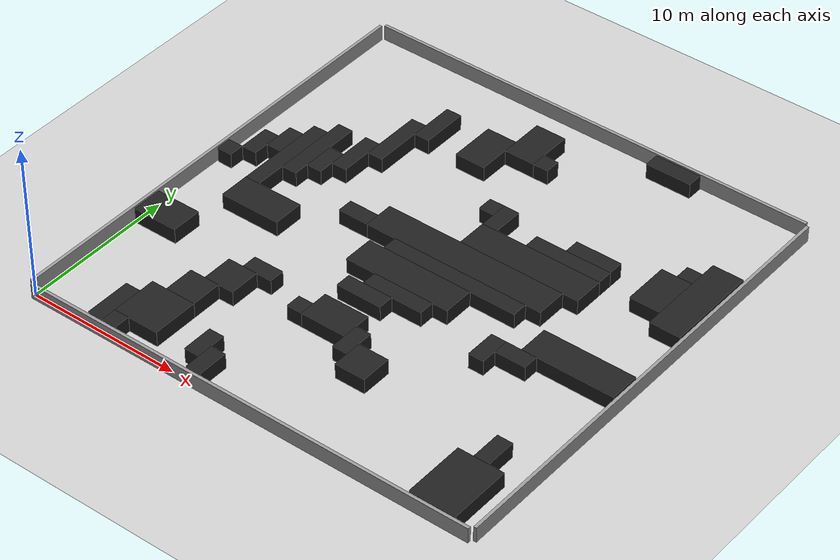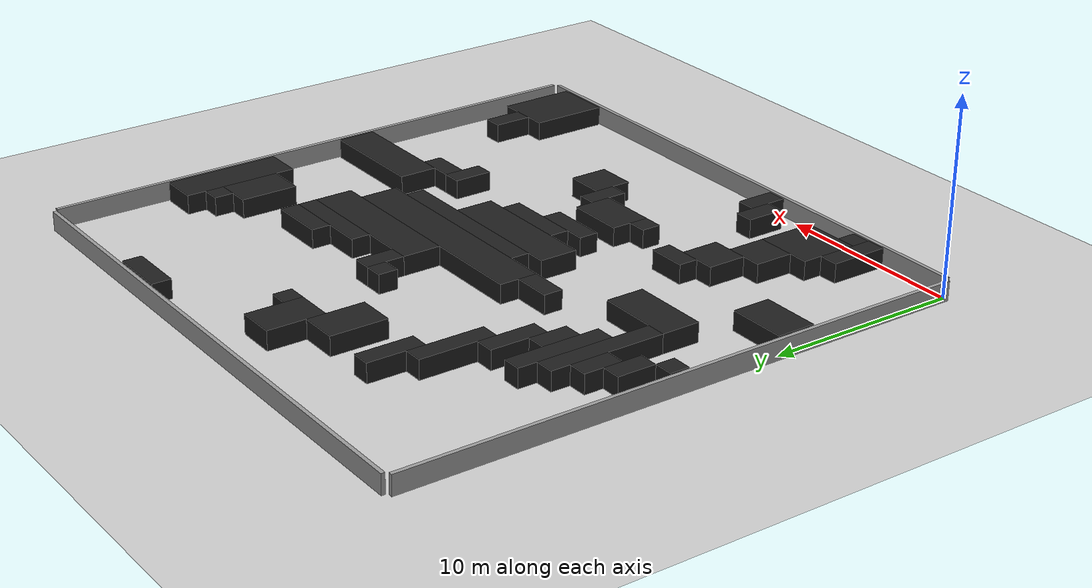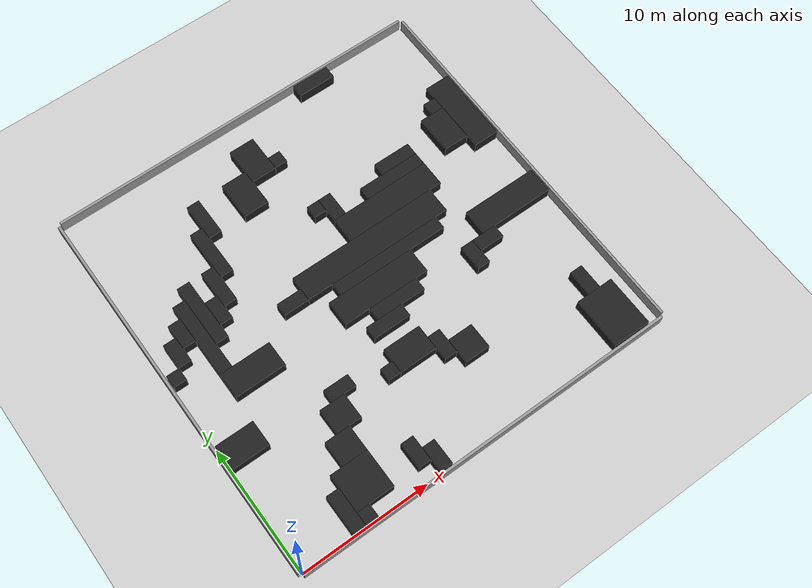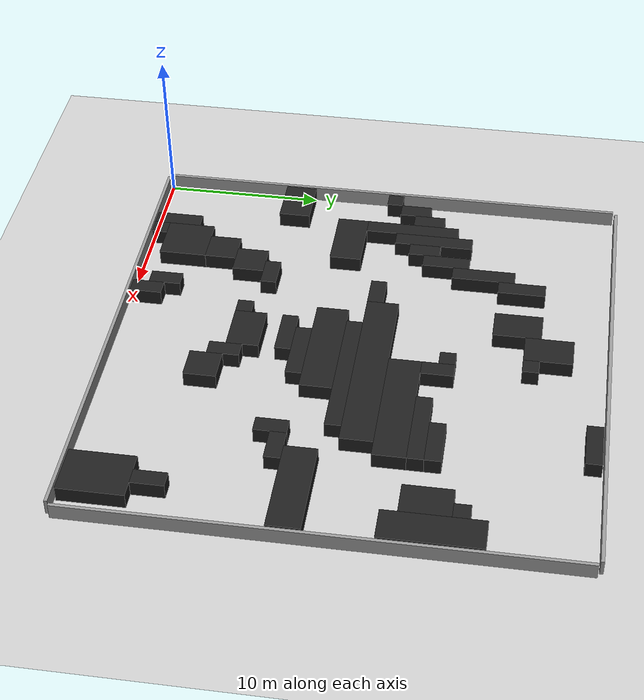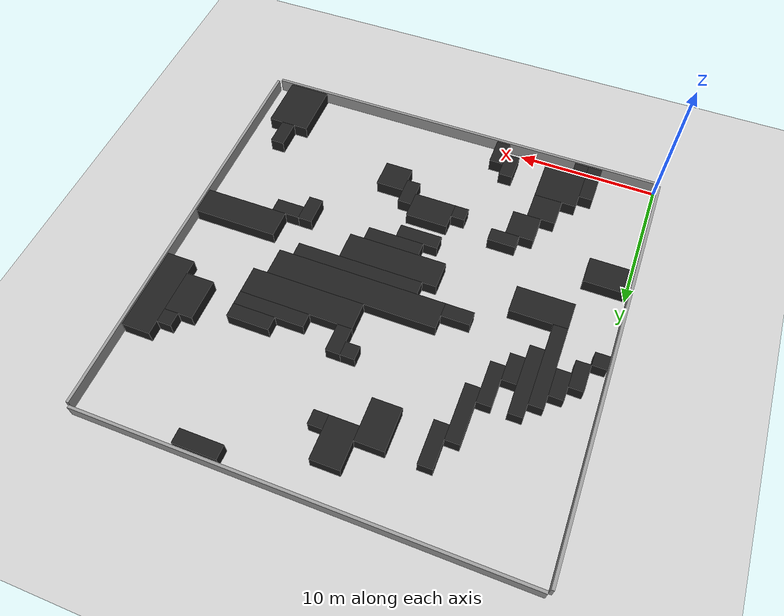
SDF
<sdf version="1.6">
 <world name="default">
  <light name="sun" type="directional">
   <pose>0 0 10 0 -0 0</pose>
   <diffuse>0.8 0.8 0.8 1</diffuse>
   <specular>0.1 0.1 0.1 1</specular>
   <attenuation>
    <range>1000</range>
    <constant>0.9</constant>
    <linear>0.01</linear>
    <quadratic>0.001</quadratic>
   </attenuation>
   <direction>-0.5 0.5 -1</direction>
  </light>
  <model name="ground_plane">
   <static>1</static>
   <link name="link">
    <collision name="collision">
     <geometry><plane><normal>0 0 1</normal><size>100 100</size></plane></geometry>
     <surface><friction><ode><mu>100</mu><mu2>50</mu2></ode></friction></surface>
    </collision>
    <visual name="visual">
     <cast_shadows>0</cast_shadows>
     <geometry><plane><normal>0 0 1</normal><size>100 100</size></plane></geometry>
     <material>
      <script><uri>file://media/materials/scripts/gazebo.material</uri><name>Gazebo/Grey</name></script>
     </material>
    </visual>
   </link>
  </model>
  <gravity>0 0 -9.8</gravity>
  <magnetic_field>6e-06 2.3e-05 -4.2e-05</magnetic_field>
  <atmosphere type="adiabatic"/>
  <physics name="default_physics" default="0" type="ode">
   <max_step_size>0.001</max_step_size>
   <real_time_factor>1</real_time_factor>
   <real_time_update_rate>1000</real_time_update_rate>
  </physics>
  <scene><ambient>0.4 0.4 0.4 1</ambient><background>0.7 0.7 0.7 1</background><shadows>1</shadows></scene>
  <spherical_coordinates>
   <surface_model>EARTH_WGS84</surface_model>
   <latitude_deg>0</latitude_deg>
   <longitude_deg>0</longitude_deg>
   <elevation>0</elevation>
   <heading_deg>0</heading_deg>
  </spherical_coordinates>
  <model name="obstacle1">
   <link name="link_0">
    <inertial>
     <mass>1</mass>
     <inertia>
      <ixx>0.166667</ixx>
      <ixy>0</ixy>
      <ixz>0</ixz>
      <iyy>0.166667</iyy>
      <iyz>0</iyz>
      <izz>0.166667</izz>
     </inertia>
    </inertial>
    <visual name="visual">
     <geometry><box><size>1 3 1</size></box></geometry>
     <material>
      <lighting>1</lighting>
      <script><uri>file://media/materials/scripts/gazebo.material</uri><name>Gazebo/Black</name></script>
      <ambient>0 0 0 1</ambient>
      <diffuse>0 0 0 1</diffuse>
      <specular>0.01 0.01 0.01 1</specular>
      <emissive>0 0 0 1</emissive>
      <shader type="vertex"><normal_map>__default__</normal_map></shader>
     </material>
    </visual>
    <collision name="collision">
     <geometry><box><size>1 3 1</size></box></geometry>
     <surface>
      <friction>
       <ode><mu>5</mu><mu2>5</mu2><fdir1>0 0 0</fdir1><slip1>0</slip1><slip2>0</slip2></ode>
       <torsional>
        <coefficient>1</coefficient>
        <patch_radius>0</patch_radius>
        <surface_radius>0</surface_radius>
        <use_patch_radius>1</use_patch_radius>
        <ode><slip>0</slip></ode>
       </torsional>
      </friction>
      <bounce><restitution_coefficient>0</restitution_coefficient><threshold>1e+06</threshold></bounce>
      <contact>
       <collide_without_contact>0</collide_without_contact>
       <collide_without_contact_bitmask>1</collide_without_contact_bitmask>
       <collide_bitmask>1</collide_bitmask>
       <ode>
        <soft_cfm>0</soft_cfm>
        <soft_erp>0.2</soft_erp>
        <kp>1e+13</kp>
        <kd>1</kd>
        <max_vel>0.01</max_vel>
        <min_depth>0</min_depth>
       </ode>
       <bullet>
        <split_impulse>1</split_impulse>
        <split_impulse_penetration_threshold>-0.01</split_impulse_penetration_threshold>
        <soft_cfm>0</soft_cfm>
        <soft_erp>0.2</soft_erp>
        <kp>1e+13</kp>
        <kd>1</kd>
       </bullet>
      </contact>
     </surface>
    </collision>
   </link>
   <static>0</static>
   <pose>4.5 1.5 0.5 0 -0 0</pose>
  </model>
  <model name="obstacle2">
   <link name="link_0">
    <inertial>
     <mass>1</mass>
     <inertia>
      <ixx>0.166667</ixx>
      <ixy>0</ixy>
      <ixz>0</ixz>
      <iyy>0.166667</iyy>
      <iyz>0</iyz>
      <izz>0.166667</izz>
     </inertia>
    </inertial>
    <visual name="visual">
     <geometry><box><size>1 1 1</size></box></geometry>
     <material>
      <lighting>1</lighting>
      <script><uri>file://media/materials/scripts/gazebo.material</uri><name>Gazebo/Black</name></script>
      <ambient>0 0 0 1</ambient>
      <diffuse>0 0 0 1</diffuse>
      <specular>0.01 0.01 0.01 1</specular>
      <emissive>0 0 0 1</emissive>
      <shader type="vertex"><normal_map>__default__</normal_map></shader>
     </material>
    </visual>
    <collision name="collision">
     <geometry><box><size>1 1 1</size></box></geometry>
     <surface>
      <friction>
       <ode><mu>5</mu><mu2>5</mu2><fdir1>0 0 0</fdir1><slip1>0</slip1><slip2>0</slip2></ode>
       <torsional>
        <coefficient>1</coefficient>
        <patch_radius>0</patch_radius>
        <surface_radius>0</surface_radius>
        <use_patch_radius>1</use_patch_radius>
        <ode><slip>0</slip></ode>
       </torsional>
      </friction>
      <bounce><restitution_coefficient>0</restitution_coefficient><threshold>1e+06</threshold></bounce>
      <contact>
       <collide_without_contact>0</collide_without_contact>
       <collide_without_contact_bitmask>1</collide_without_contact_bitmask>
       <collide_bitmask>1</collide_bitmask>
       <ode>
        <soft_cfm>0</soft_cfm>
        <soft_erp>0.2</soft_erp>
        <kp>1e+13</kp>
        <kd>1</kd>
        <max_vel>0.01</max_vel>
        <min_depth>0</min_depth>
       </ode>
       <bullet>
        <split_impulse>1</split_impulse>
        <split_impulse_penetration_threshold>-0.01</split_impulse_penetration_threshold>
        <soft_cfm>0</soft_cfm>
        <soft_erp>0.2</soft_erp>
        <kp>1e+13</kp>
        <kd>1</kd>
       </bullet>
      </contact>
     </surface>
    </collision>
   </link>
   <static>0</static>
   <pose>5.5 0.5 0.5 0 -0 0</pose>
  </model>
  <model name="obstacle3">
   <link name="link_0">
    <inertial>
     <mass>1</mass>
     <inertia>
      <ixx>0.166667</ixx>
      <ixy>0</ixy>
      <ixz>0</ixz>
      <iyy>0.166667</iyy>
      <iyz>0</iyz>
      <izz>0.166667</izz>
     </inertia>
    </inertial>
    <visual name="visual">
     <geometry><box><size>3 3 1</size></box></geometry>
     <material>
      <lighting>1</lighting>
      <script><uri>file://media/materials/scripts/gazebo.material</uri><name>Gazebo/Black</name></script>
      <ambient>0 0 0 1</ambient>
      <diffuse>0 0 0 1</diffuse>
      <specular>0.01 0.01 0.01 1</specular>
      <emissive>0 0 0 1</emissive>
      <shader type="vertex"><normal_map>__default__</normal_map></shader>
     </material>
    </visual>
    <collision name="collision">
     <geometry><box><size>3 3 1</size></box></geometry>
     <surface>
      <friction>
       <ode><mu>5</mu><mu2>5</mu2><fdir1>0 0 0</fdir1><slip1>0</slip1><slip2>0</slip2></ode>
       <torsional>
        <coefficient>1</coefficient>
        <patch_radius>0</patch_radius>
        <surface_radius>0</surface_radius>
        <use_patch_radius>1</use_patch_radius>
        <ode><slip>0</slip></ode>
       </torsional>
      </friction>
      <bounce><restitution_coefficient>0</restitution_coefficient><threshold>1e+06</threshold></bounce>
      <contact>
       <collide_without_contact>0</collide_without_contact>
       <collide_without_contact_bitmask>1</collide_without_contact_bitmask>
       <collide_bitmask>1</collide_bitmask>
       <ode>
        <soft_cfm>0</soft_cfm>
        <soft_erp>0.2</soft_erp>
        <kp>1e+13</kp>
        <kd>1</kd>
        <max_vel>0.01</max_vel>
        <min_depth>0</min_depth>
       </ode>
       <bullet>
        <split_impulse>1</split_impulse>
        <split_impulse_penetration_threshold>-0.01</split_impulse_penetration_threshold>
        <soft_cfm>0</soft_cfm>
        <soft_erp>0.2</soft_erp>
        <kp>1e+13</kp>
        <kd>1</kd>
       </bullet>
      </contact>
     </surface>
    </collision>
   </link>
   <static>0</static>
   <pose>6.5 2.5 0.5 0 -0 0</pose>
  </model>
  <model name="obstacle4">
   <link name="link_0">
    <inertial>
     <mass>1</mass>
     <inertia>
      <ixx>0.166667</ixx>
      <ixy>0</ixy>
      <ixz>0</ixz>
      <iyy>0.166667</iyy>
      <iyz>0</iyz>
      <izz>0.166667</izz>
     </inertia>
    </inertial>
    <visual name="visual">
     <geometry><box><size>2 2 1</size></box></geometry>
     <material>
      <lighting>1</lighting>
      <script><uri>file://media/materials/scripts/gazebo.material</uri><name>Gazebo/Black</name></script>
      <ambient>0 0 0 1</ambient>
      <diffuse>0 0 0 1</diffuse>
      <specular>0.01 0.01 0.01 1</specular>
      <emissive>0 0 0 1</emissive>
      <shader type="vertex"><normal_map>__default__</normal_map></shader>
     </material>
    </visual>
    <collision name="collision">
     <geometry><box><size>2 2 1</size></box></geometry>
     <surface>
      <friction>
       <ode><mu>5</mu><mu2>5</mu2><fdir1>0 0 0</fdir1><slip1>0</slip1><slip2>0</slip2></ode>
       <torsional>
        <coefficient>1</coefficient>
        <patch_radius>0</patch_radius>
        <surface_radius>0</surface_radius>
        <use_patch_radius>1</use_patch_radius>
        <ode><slip>0</slip></ode>
       </torsional>
      </friction>
      <bounce><restitution_coefficient>0</restitution_coefficient><threshold>1e+06</threshold></bounce>
      <contact>
       <collide_without_contact>0</collide_without_contact>
       <collide_without_contact_bitmask>1</collide_without_contact_bitmask>
       <collide_bitmask>1</collide_bitmask>
       <ode>
        <soft_cfm>0</soft_cfm>
        <soft_erp>0.2</soft_erp>
        <kp>1e+13</kp>
        <kd>1</kd>
        <max_vel>0.01</max_vel>
        <min_depth>0</min_depth>
       </ode>
       <bullet>
        <split_impulse>1</split_impulse>
        <split_impulse_penetration_threshold>-0.01</split_impulse_penetration_threshold>
        <soft_cfm>0</soft_cfm>
        <soft_erp>0.2</soft_erp>
        <kp>1e+13</kp>
        <kd>1</kd>
       </bullet>
      </contact>
     </surface>
    </collision>
   </link>
   <static>0</static>
   <pose>7.0 5.0 0.5 0 -0 0</pose>
  </model>
  <model name="obstacle5">
   <link name="link_0">
    <inertial>
     <mass>1</mass>
     <inertia>
      <ixx>0.166667</ixx>
      <ixy>0</ixy>
      <ixz>0</ixz>
      <iyy>0.166667</iyy>
      <iyz>0</iyz>
      <izz>0.166667</izz>
     </inertia>
    </inertial>
    <visual name="visual">
     <geometry><box><size>2 2 1</size></box></geometry>
     <material>
      <lighting>1</lighting>
      <script><uri>file://media/materials/scripts/gazebo.material</uri><name>Gazebo/Black</name></script>
      <ambient>0 0 0 1</ambient>
      <diffuse>0 0 0 1</diffuse>
      <specular>0.01 0.01 0.01 1</specular>
      <emissive>0 0 0 1</emissive>
      <shader type="vertex"><normal_map>__default__</normal_map></shader>
     </material>
    </visual>
    <collision name="collision">
     <geometry><box><size>2 2 1</size></box></geometry>
     <surface>
      <friction>
       <ode><mu>5</mu><mu2>5</mu2><fdir1>0 0 0</fdir1><slip1>0</slip1><slip2>0</slip2></ode>
       <torsional>
        <coefficient>1</coefficient>
        <patch_radius>0</patch_radius>
        <surface_radius>0</surface_radius>
        <use_patch_radius>1</use_patch_radius>
        <ode><slip>0</slip></ode>
       </torsional>
      </friction>
      <bounce><restitution_coefficient>0</restitution_coefficient><threshold>1e+06</threshold></bounce>
      <contact>
       <collide_without_contact>0</collide_without_contact>
       <collide_without_contact_bitmask>1</collide_without_contact_bitmask>
       <collide_bitmask>1</collide_bitmask>
       <ode>
        <soft_cfm>0</soft_cfm>
        <soft_erp>0.2</soft_erp>
        <kp>1e+13</kp>
        <kd>1</kd>
        <max_vel>0.01</max_vel>
        <min_depth>0</min_depth>
       </ode>
       <bullet>
        <split_impulse>1</split_impulse>
        <split_impulse_penetration_threshold>-0.01</split_impulse_penetration_threshold>
        <soft_cfm>0</soft_cfm>
        <soft_erp>0.2</soft_erp>
        <kp>1e+13</kp>
        <kd>1</kd>
       </bullet>
      </contact>
     </surface>
    </collision>
   </link>
   <static>0</static>
   <pose>8.0 7.0 0.5 0 -0 0</pose>
  </model>
  <model name="obstacle6">
   <link name="link_0">
    <inertial>
     <mass>1</mass>
     <inertia>
      <ixx>0.166667</ixx>
      <ixy>0</ixy>
      <ixz>0</ixz>
      <iyy>0.166667</iyy>
      <iyz>0</iyz>
      <izz>0.166667</izz>
     </inertia>
    </inertial>
    <visual name="visual">
     <geometry><box><size>2 1 1</size></box></geometry>
     <material>
      <lighting>1</lighting>
      <script><uri>file://media/materials/scripts/gazebo.material</uri><name>Gazebo/Black</name></script>
      <ambient>0 0 0 1</ambient>
      <diffuse>0 0 0 1</diffuse>
      <specular>0.01 0.01 0.01 1</specular>
      <emissive>0 0 0 1</emissive>
      <shader type="vertex"><normal_map>__default__</normal_map></shader>
     </material>
    </visual>
    <collision name="collision">
     <geometry><box><size>2 1 1</size></box></geometry>
     <surface>
      <friction>
       <ode><mu>5</mu><mu2>5</mu2><fdir1>0 0 0</fdir1><slip1>0</slip1><slip2>0</slip2></ode>
       <torsional>
        <coefficient>1</coefficient>
        <patch_radius>0</patch_radius>
        <surface_radius>0</surface_radius>
        <use_patch_radius>1</use_patch_radius>
        <ode><slip>0</slip></ode>
       </torsional>
      </friction>
      <bounce><restitution_coefficient>0</restitution_coefficient><threshold>1e+06</threshold></bounce>
      <contact>
       <collide_without_contact>0</collide_without_contact>
       <collide_without_contact_bitmask>1</collide_without_contact_bitmask>
       <collide_bitmask>1</collide_bitmask>
       <ode>
        <soft_cfm>0</soft_cfm>
        <soft_erp>0.2</soft_erp>
        <kp>1e+13</kp>
        <kd>1</kd>
        <max_vel>0.01</max_vel>
        <min_depth>0</min_depth>
       </ode>
       <bullet>
        <split_impulse>1</split_impulse>
        <split_impulse_penetration_threshold>-0.01</split_impulse_penetration_threshold>
        <soft_cfm>0</soft_cfm>
        <soft_erp>0.2</soft_erp>
        <kp>1e+13</kp>
        <kd>1</kd>
       </bullet>
      </contact>
     </surface>
    </collision>
   </link>
   <static>0</static>
   <pose>9.0 8.5 0.5 0 -0 0</pose>
  </model>
  <model name="obstacle7">
   <link name="link_0">
    <inertial>
     <mass>1</mass>
     <inertia>
      <ixx>0.166667</ixx>
      <ixy>0</ixy>
      <ixz>0</ixz>
      <iyy>0.166667</iyy>
      <iyz>0</iyz>
      <izz>0.166667</izz>
     </inertia>
    </inertial>
    <visual name="visual">
     <geometry><box><size>1 2 1</size></box></geometry>
     <material>
      <lighting>1</lighting>
      <script><uri>file://media/materials/scripts/gazebo.material</uri><name>Gazebo/Black</name></script>
      <ambient>0 0 0 1</ambient>
      <diffuse>0 0 0 1</diffuse>
      <specular>0.01 0.01 0.01 1</specular>
      <emissive>0 0 0 1</emissive>
      <shader type="vertex"><normal_map>__default__</normal_map></shader>
     </material>
    </visual>
    <collision name="collision">
     <geometry><box><size>1 2 1</size></box></geometry>
     <surface>
      <friction>
       <ode><mu>5</mu><mu2>5</mu2><fdir1>0 0 0</fdir1><slip1>0</slip1><slip2>0</slip2></ode>
       <torsional>
        <coefficient>1</coefficient>
        <patch_radius>0</patch_radius>
        <surface_radius>0</surface_radius>
        <use_patch_radius>1</use_patch_radius>
        <ode><slip>0</slip></ode>
       </torsional>
      </friction>
      <bounce><restitution_coefficient>0</restitution_coefficient><threshold>1e+06</threshold></bounce>
      <contact>
       <collide_without_contact>0</collide_without_contact>
       <collide_without_contact_bitmask>1</collide_without_contact_bitmask>
       <collide_bitmask>1</collide_bitmask>
       <ode>
        <soft_cfm>0</soft_cfm>
        <soft_erp>0.2</soft_erp>
        <kp>1e+13</kp>
        <kd>1</kd>
        <max_vel>0.01</max_vel>
        <min_depth>0</min_depth>
       </ode>
       <bullet>
        <split_impulse>1</split_impulse>
        <split_impulse_penetration_threshold>-0.01</split_impulse_penetration_threshold>
        <soft_cfm>0</soft_cfm>
        <soft_erp>0.2</soft_erp>
        <kp>1e+13</kp>
        <kd>1</kd>
       </bullet>
      </contact>
     </surface>
    </collision>
   </link>
   <static>0</static>
   <pose>10.5 2.0 0.5 0 -0 0</pose>
  </model>
  <model name="obstacle8">
   <link name="link_0">
    <inertial>
     <mass>1</mass>
     <inertia>
      <ixx>0.166667</ixx>
      <ixy>0</ixy>
      <ixz>0</ixz>
      <iyy>0.166667</iyy>
      <iyz>0</iyz>
      <izz>0.166667</izz>
     </inertia>
    </inertial>
    <visual name="visual">
     <geometry><box><size>1 2 1</size></box></geometry>
     <material>
      <lighting>1</lighting>
      <script><uri>file://media/materials/scripts/gazebo.material</uri><name>Gazebo/Black</name></script>
      <ambient>0 0 0 1</ambient>
      <diffuse>0 0 0 1</diffuse>
      <specular>0.01 0.01 0.01 1</specular>
      <emissive>0 0 0 1</emissive>
      <shader type="vertex"><normal_map>__default__</normal_map></shader>
     </material>
    </visual>
    <collision name="collision">
     <geometry><box><size>1 2 1</size></box></geometry>
     <surface>
      <friction>
       <ode><mu>5</mu><mu2>5</mu2><fdir1>0 0 0</fdir1><slip1>0</slip1><slip2>0</slip2></ode>
       <torsional>
        <coefficient>1</coefficient>
        <patch_radius>0</patch_radius>
        <surface_radius>0</surface_radius>
        <use_patch_radius>1</use_patch_radius>
        <ode><slip>0</slip></ode>
       </torsional>
      </friction>
      <bounce><restitution_coefficient>0</restitution_coefficient><threshold>1e+06</threshold></bounce>
      <contact>
       <collide_without_contact>0</collide_without_contact>
       <collide_without_contact_bitmask>1</collide_without_contact_bitmask>
       <collide_bitmask>1</collide_bitmask>
       <ode>
        <soft_cfm>0</soft_cfm>
        <soft_erp>0.2</soft_erp>
        <kp>1e+13</kp>
        <kd>1</kd>
        <max_vel>0.01</max_vel>
        <min_depth>0</min_depth>
       </ode>
       <bullet>
        <split_impulse>1</split_impulse>
        <split_impulse_penetration_threshold>-0.01</split_impulse_penetration_threshold>
        <soft_cfm>0</soft_cfm>
        <soft_erp>0.2</soft_erp>
        <kp>1e+13</kp>
        <kd>1</kd>
       </bullet>
      </contact>
     </surface>
    </collision>
   </link>
   <static>0</static>
   <pose>11.5 1.0 0.5 0 -0 0</pose>
  </model>
  <model name="obstacle9">
   <link name="link_0">
    <inertial>
     <mass>1</mass>
     <inertia>
      <ixx>0.166667</ixx>
      <ixy>0</ixy>
      <ixz>0</ixz>
      <iyy>0.166667</iyy>
      <iyz>0</iyz>
      <izz>0.166667</izz>
     </inertia>
    </inertial>
    <visual name="visual">
     <geometry><box><size>3 4 1</size></box></geometry>
     <material>
      <lighting>1</lighting>
      <script><uri>file://media/materials/scripts/gazebo.material</uri><name>Gazebo/Black</name></script>
      <ambient>0 0 0 1</ambient>
      <diffuse>0 0 0 1</diffuse>
      <specular>0.01 0.01 0.01 1</specular>
      <emissive>0 0 0 1</emissive>
      <shader type="vertex"><normal_map>__default__</normal_map></shader>
     </material>
    </visual>
    <collision name="collision">
     <geometry><box><size>3 4 1</size></box></geometry>
     <surface>
      <friction>
       <ode><mu>5</mu><mu2>5</mu2><fdir1>0 0 0</fdir1><slip1>0</slip1><slip2>0</slip2></ode>
       <torsional>
        <coefficient>1</coefficient>
        <patch_radius>0</patch_radius>
        <surface_radius>0</surface_radius>
        <use_patch_radius>1</use_patch_radius>
        <ode><slip>0</slip></ode>
       </torsional>
      </friction>
      <bounce><restitution_coefficient>0</restitution_coefficient><threshold>1e+06</threshold></bounce>
      <contact>
       <collide_without_contact>0</collide_without_contact>
       <collide_without_contact_bitmask>1</collide_without_contact_bitmask>
       <collide_bitmask>1</collide_bitmask>
       <ode>
        <soft_cfm>0</soft_cfm>
        <soft_erp>0.2</soft_erp>
        <kp>1e+13</kp>
        <kd>1</kd>
        <max_vel>0.01</max_vel>
        <min_depth>0</min_depth>
       </ode>
       <bullet>
        <split_impulse>1</split_impulse>
        <split_impulse_penetration_threshold>-0.01</split_impulse_penetration_threshold>
        <soft_cfm>0</soft_cfm>
        <soft_erp>0.2</soft_erp>
        <kp>1e+13</kp>
        <kd>1</kd>
       </bullet>
      </contact>
     </surface>
    </collision>
   </link>
   <static>0</static>
   <pose>27.5 2.0 0.5 0 -0 0</pose>
  </model>
  <model name="obstacle10">
   <link name="link_0">
    <inertial>
     <mass>1</mass>
     <inertia>
      <ixx>0.166667</ixx>
      <ixy>0</ixy>
      <ixz>0</ixz>
      <iyy>0.166667</iyy>
      <iyz>0</iyz>
      <izz>0.166667</izz>
     </inertia>
    </inertial>
    <visual name="visual">
     <geometry><box><size>1 2 1</size></box></geometry>
     <material>
      <lighting>1</lighting>
      <script><uri>file://media/materials/scripts/gazebo.material</uri><name>Gazebo/Black</name></script>
      <ambient>0 0 0 1</ambient>
      <diffuse>0 0 0 1</diffuse>
      <specular>0.01 0.01 0.01 1</specular>
      <emissive>0 0 0 1</emissive>
      <shader type="vertex"><normal_map>__default__</normal_map></shader>
     </material>
    </visual>
    <collision name="collision">
     <geometry><box><size>1 2 1</size></box></geometry>
     <surface>
      <friction>
       <ode><mu>5</mu><mu2>5</mu2><fdir1>0 0 0</fdir1><slip1>0</slip1><slip2>0</slip2></ode>
       <torsional>
        <coefficient>1</coefficient>
        <patch_radius>0</patch_radius>
        <surface_radius>0</surface_radius>
        <use_patch_radius>1</use_patch_radius>
        <ode><slip>0</slip></ode>
       </torsional>
      </friction>
      <bounce><restitution_coefficient>0</restitution_coefficient><threshold>1e+06</threshold></bounce>
      <contact>
       <collide_without_contact>0</collide_without_contact>
       <collide_without_contact_bitmask>1</collide_without_contact_bitmask>
       <collide_bitmask>1</collide_bitmask>
       <ode>
        <soft_cfm>0</soft_cfm>
        <soft_erp>0.2</soft_erp>
        <kp>1e+13</kp>
        <kd>1</kd>
        <max_vel>0.01</max_vel>
        <min_depth>0</min_depth>
       </ode>
       <bullet>
        <split_impulse>1</split_impulse>
        <split_impulse_penetration_threshold>-0.01</split_impulse_penetration_threshold>
        <soft_cfm>0</soft_cfm>
        <soft_erp>0.2</soft_erp>
        <kp>1e+13</kp>
        <kd>1</kd>
       </bullet>
      </contact>
     </surface>
    </collision>
   </link>
   <static>0</static>
   <pose>27.5 5.0 0.5 0 -0 0</pose>
  </model>
  <model name="obstacle11">
   <link name="link_0">
    <inertial>
     <mass>1</mass>
     <inertia>
      <ixx>0.166667</ixx>
      <ixy>0</ixy>
      <ixz>0</ixz>
      <iyy>0.166667</iyy>
      <iyz>0</iyz>
      <izz>0.166667</izz>
     </inertia>
    </inertial>
    <visual name="visual">
     <geometry><box><size>3 2 1</size></box></geometry>
     <material>
      <lighting>1</lighting>
      <script><uri>file://media/materials/scripts/gazebo.material</uri><name>Gazebo/Black</name></script>
      <ambient>0 0 0 1</ambient>
      <diffuse>0 0 0 1</diffuse>
      <specular>0.01 0.01 0.01 1</specular>
      <emissive>0 0 0 1</emissive>
      <shader type="vertex"><normal_map>__default__</normal_map></shader>
     </material>
    </visual>
    <collision name="collision">
     <geometry><box><size>3 2 1</size></box></geometry>
     <surface>
      <friction>
       <ode><mu>5</mu><mu2>5</mu2><fdir1>0 0 0</fdir1><slip1>0</slip1><slip2>0</slip2></ode>
       <torsional>
        <coefficient>1</coefficient>
        <patch_radius>0</patch_radius>
        <surface_radius>0</surface_radius>
        <use_patch_radius>1</use_patch_radius>
        <ode><slip>0</slip></ode>
       </torsional>
      </friction>
      <bounce><restitution_coefficient>0</restitution_coefficient><threshold>1e+06</threshold></bounce>
      <contact>
       <collide_without_contact>0</collide_without_contact>
       <collide_without_contact_bitmask>1</collide_without_contact_bitmask>
       <collide_bitmask>1</collide_bitmask>
       <ode>
        <soft_cfm>0</soft_cfm>
        <soft_erp>0.2</soft_erp>
        <kp>1e+13</kp>
        <kd>1</kd>
        <max_vel>0.01</max_vel>
        <min_depth>0</min_depth>
       </ode>
       <bullet>
        <split_impulse>1</split_impulse>
        <split_impulse_penetration_threshold>-0.01</split_impulse_penetration_threshold>
        <soft_cfm>0</soft_cfm>
        <soft_erp>0.2</soft_erp>
        <kp>1e+13</kp>
        <kd>1</kd>
       </bullet>
      </contact>
     </surface>
    </collision>
   </link>
   <static>0</static>
   <pose>1.5 9.0 0.5 0 -0 0</pose>
  </model>
  <model name="obstacle12">
   <link name="link_0">
    <inertial>
     <mass>1</mass>
     <inertia>
      <ixx>0.166667</ixx>
      <ixy>0</ixy>
      <ixz>0</ixz>
      <iyy>0.166667</iyy>
      <iyz>0</iyz>
      <izz>0.166667</izz>
     </inertia>
    </inertial>
    <visual name="visual">
     <geometry><box><size>1 1 1</size></box></geometry>
     <material>
      <lighting>1</lighting>
      <script><uri>file://media/materials/scripts/gazebo.material</uri><name>Gazebo/Black</name></script>
      <ambient>0 0 0 1</ambient>
      <diffuse>0 0 0 1</diffuse>
      <specular>0.01 0.01 0.01 1</specular>
      <emissive>0 0 0 1</emissive>
      <shader type="vertex"><normal_map>__default__</normal_map></shader>
     </material>
    </visual>
    <collision name="collision">
     <geometry><box><size>1 1 1</size></box></geometry>
     <surface>
      <friction>
       <ode><mu>5</mu><mu2>5</mu2><fdir1>0 0 0</fdir1><slip1>0</slip1><slip2>0</slip2></ode>
       <torsional>
        <coefficient>1</coefficient>
        <patch_radius>0</patch_radius>
        <surface_radius>0</surface_radius>
        <use_patch_radius>1</use_patch_radius>
        <ode><slip>0</slip></ode>
       </torsional>
      </friction>
      <bounce><restitution_coefficient>0</restitution_coefficient><threshold>1e+06</threshold></bounce>
      <contact>
       <collide_without_contact>0</collide_without_contact>
       <collide_without_contact_bitmask>1</collide_without_contact_bitmask>
       <collide_bitmask>1</collide_bitmask>
       <ode>
        <soft_cfm>0</soft_cfm>
        <soft_erp>0.2</soft_erp>
        <kp>1e+13</kp>
        <kd>1</kd>
        <max_vel>0.01</max_vel>
        <min_depth>0</min_depth>
       </ode>
       <bullet>
        <split_impulse>1</split_impulse>
        <split_impulse_penetration_threshold>-0.01</split_impulse_penetration_threshold>
        <soft_cfm>0</soft_cfm>
        <soft_erp>0.2</soft_erp>
        <kp>1e+13</kp>
        <kd>1</kd>
       </bullet>
      </contact>
     </surface>
    </collision>
   </link>
   <static>0</static>
   <pose>12.5 7.5 0.5 0 -0 0</pose>
  </model>
  <model name="obstacle13">
   <link name="link_0">
    <inertial>
     <mass>1</mass>
     <inertia>
      <ixx>0.166667</ixx>
      <ixy>0</ixy>
      <ixz>0</ixz>
      <iyy>0.166667</iyy>
      <iyz>0</iyz>
      <izz>0.166667</izz>
     </inertia>
    </inertial>
    <visual name="visual">
     <geometry><box><size>3 2 1</size></box></geometry>
     <material>
      <lighting>1</lighting>
      <script><uri>file://media/materials/scripts/gazebo.material</uri><name>Gazebo/Black</name></script>
      <ambient>0 0 0 1</ambient>
      <diffuse>0 0 0 1</diffuse>
      <specular>0.01 0.01 0.01 1</specular>
      <emissive>0 0 0 1</emissive>
      <shader type="vertex"><normal_map>__default__</normal_map></shader>
     </material>
    </visual>
    <collision name="collision">
     <geometry><box><size>3 2 1</size></box></geometry>
     <surface>
      <friction>
       <ode><mu>5</mu><mu2>5</mu2><fdir1>0 0 0</fdir1><slip1>0</slip1><slip2>0</slip2></ode>
       <torsional>
        <coefficient>1</coefficient>
        <patch_radius>0</patch_radius>
        <surface_radius>0</surface_radius>
        <use_patch_radius>1</use_patch_radius>
        <ode><slip>0</slip></ode>
       </torsional>
      </friction>
      <bounce><restitution_coefficient>0</restitution_coefficient><threshold>1e+06</threshold></bounce>
      <contact>
       <collide_without_contact>0</collide_without_contact>
       <collide_without_contact_bitmask>1</collide_without_contact_bitmask>
       <collide_bitmask>1</collide_bitmask>
       <ode>
        <soft_cfm>0</soft_cfm>
        <soft_erp>0.2</soft_erp>
        <kp>1e+13</kp>
        <kd>1</kd>
        <max_vel>0.01</max_vel>
        <min_depth>0</min_depth>
       </ode>
       <bullet>
        <split_impulse>1</split_impulse>
        <split_impulse_penetration_threshold>-0.01</split_impulse_penetration_threshold>
        <soft_cfm>0</soft_cfm>
        <soft_erp>0.2</soft_erp>
        <kp>1e+13</kp>
        <kd>1</kd>
       </bullet>
      </contact>
     </surface>
    </collision>
   </link>
   <static>0</static>
   <pose>14.5 8.0 0.5 0 -0 0</pose>
  </model>
  <model name="obstacle14">
   <link name="link_0">
    <inertial>
     <mass>1</mass>
     <inertia>
      <ixx>0.166667</ixx>
      <ixy>0</ixy>
      <ixz>0</ixz>
      <iyy>0.166667</iyy>
      <iyz>0</iyz>
      <izz>0.166667</izz>
     </inertia>
    </inertial>
    <visual name="visual">
     <geometry><box><size>1 2 1</size></box></geometry>
     <material>
      <lighting>1</lighting>
      <script><uri>file://media/materials/scripts/gazebo.material</uri><name>Gazebo/Black</name></script>
      <ambient>0 0 0 1</ambient>
      <diffuse>0 0 0 1</diffuse>
      <specular>0.01 0.01 0.01 1</specular>
      <emissive>0 0 0 1</emissive>
      <shader type="vertex"><normal_map>__default__</normal_map></shader>
     </material>
    </visual>
    <collision name="collision">
     <geometry><box><size>1 2 1</size></box></geometry>
     <surface>
      <friction>
       <ode><mu>5</mu><mu2>5</mu2><fdir1>0 0 0</fdir1><slip1>0</slip1><slip2>0</slip2></ode>
       <torsional>
        <coefficient>1</coefficient>
        <patch_radius>0</patch_radius>
        <surface_radius>0</surface_radius>
        <use_patch_radius>1</use_patch_radius>
        <ode><slip>0</slip></ode>
       </torsional>
      </friction>
      <bounce><restitution_coefficient>0</restitution_coefficient><threshold>1e+06</threshold></bounce>
      <contact>
       <collide_without_contact>0</collide_without_contact>
       <collide_without_contact_bitmask>1</collide_without_contact_bitmask>
       <collide_bitmask>1</collide_bitmask>
       <ode>
        <soft_cfm>0</soft_cfm>
        <soft_erp>0.2</soft_erp>
        <kp>1e+13</kp>
        <kd>1</kd>
        <max_vel>0.01</max_vel>
        <min_depth>0</min_depth>
       </ode>
       <bullet>
        <split_impulse>1</split_impulse>
        <split_impulse_penetration_threshold>-0.01</split_impulse_penetration_threshold>
        <soft_cfm>0</soft_cfm>
        <soft_erp>0.2</soft_erp>
        <kp>1e+13</kp>
        <kd>1</kd>
       </bullet>
      </contact>
     </surface>
    </collision>
   </link>
   <static>0</static>
   <pose>16.5 7.0 0.5 0 -0 0</pose>
  </model>
  <model name="obstacle15">
   <link name="link_0">
    <inertial>
     <mass>1</mass>
     <inertia>
      <ixx>0.166667</ixx>
      <ixy>0</ixy>
      <ixz>0</ixz>
      <iyy>0.166667</iyy>
      <iyz>0</iyz>
      <izz>0.166667</izz>
     </inertia>
    </inertial>
    <visual name="visual">
     <geometry><box><size>2 2 1</size></box></geometry>
     <material>
      <lighting>1</lighting>
      <script><uri>file://media/materials/scripts/gazebo.material</uri><name>Gazebo/Black</name></script>
      <ambient>0 0 0 1</ambient>
      <diffuse>0 0 0 1</diffuse>
      <specular>0.01 0.01 0.01 1</specular>
      <emissive>0 0 0 1</emissive>
      <shader type="vertex"><normal_map>__default__</normal_map></shader>
     </material>
    </visual>
    <collision name="collision">
     <geometry><box><size>2 2 1</size></box></geometry>
     <surface>
      <friction>
       <ode><mu>5</mu><mu2>5</mu2><fdir1>0 0 0</fdir1><slip1>0</slip1><slip2>0</slip2></ode>
       <torsional>
        <coefficient>1</coefficient>
        <patch_radius>0</patch_radius>
        <surface_radius>0</surface_radius>
        <use_patch_radius>1</use_patch_radius>
        <ode><slip>0</slip></ode>
       </torsional>
      </friction>
      <bounce><restitution_coefficient>0</restitution_coefficient><threshold>1e+06</threshold></bounce>
      <contact>
       <collide_without_contact>0</collide_without_contact>
       <collide_without_contact_bitmask>1</collide_without_contact_bitmask>
       <collide_bitmask>1</collide_bitmask>
       <ode>
        <soft_cfm>0</soft_cfm>
        <soft_erp>0.2</soft_erp>
        <kp>1e+13</kp>
        <kd>1</kd>
        <max_vel>0.01</max_vel>
        <min_depth>0</min_depth>
       </ode>
       <bullet>
        <split_impulse>1</split_impulse>
        <split_impulse_penetration_threshold>-0.01</split_impulse_penetration_threshold>
        <soft_cfm>0</soft_cfm>
        <soft_erp>0.2</soft_erp>
        <kp>1e+13</kp>
        <kd>1</kd>
       </bullet>
      </contact>
     </surface>
    </collision>
   </link>
   <static>0</static>
   <pose>18.0 6.0 0.5 0 -0 0</pose>
  </model>
  <model name="obstacle16">
   <link name="link_0">
    <inertial>
     <mass>1</mass>
     <inertia>
      <ixx>0.166667</ixx>
      <ixy>0</ixy>
      <ixz>0</ixz>
      <iyy>0.166667</iyy>
      <iyz>0</iyz>
      <izz>0.166667</izz>
     </inertia>
    </inertial>
    <visual name="visual">
     <geometry><box><size>1 1 1</size></box></geometry>
     <material>
      <lighting>1</lighting>
      <script><uri>file://media/materials/scripts/gazebo.material</uri><name>Gazebo/Black</name></script>
      <ambient>0 0 0 1</ambient>
      <diffuse>0 0 0 1</diffuse>
      <specular>0.01 0.01 0.01 1</specular>
      <emissive>0 0 0 1</emissive>
      <shader type="vertex"><normal_map>__default__</normal_map></shader>
     </material>
    </visual>
    <collision name="collision">
     <geometry><box><size>1 1 1</size></box></geometry>
     <surface>
      <friction>
       <ode><mu>5</mu><mu2>5</mu2><fdir1>0 0 0</fdir1><slip1>0</slip1><slip2>0</slip2></ode>
       <torsional>
        <coefficient>1</coefficient>
        <patch_radius>0</patch_radius>
        <surface_radius>0</surface_radius>
        <use_patch_radius>1</use_patch_radius>
        <ode><slip>0</slip></ode>
       </torsional>
      </friction>
      <bounce><restitution_coefficient>0</restitution_coefficient><threshold>1e+06</threshold></bounce>
      <contact>
       <collide_without_contact>0</collide_without_contact>
       <collide_without_contact_bitmask>1</collide_without_contact_bitmask>
       <collide_bitmask>1</collide_bitmask>
       <ode>
        <soft_cfm>0</soft_cfm>
        <soft_erp>0.2</soft_erp>
        <kp>1e+13</kp>
        <kd>1</kd>
        <max_vel>0.01</max_vel>
        <min_depth>0</min_depth>
       </ode>
       <bullet>
        <split_impulse>1</split_impulse>
        <split_impulse_penetration_threshold>-0.01</split_impulse_penetration_threshold>
        <soft_cfm>0</soft_cfm>
        <soft_erp>0.2</soft_erp>
        <kp>1e+13</kp>
        <kd>1</kd>
       </bullet>
      </contact>
     </surface>
    </collision>
   </link>
   <static>0</static>
   <pose>0.5 15.5 0.5 0 -0 0</pose>
  </model>
  <model name="obstacle17">
   <link name="link_0">
    <inertial>
     <mass>1</mass>
     <inertia>
      <ixx>0.166667</ixx>
      <ixy>0</ixy>
      <ixz>0</ixz>
      <iyy>0.166667</iyy>
      <iyz>0</iyz>
      <izz>0.166667</izz>
     </inertia>
    </inertial>
    <visual name="visual">
     <geometry><box><size>1 2 1</size></box></geometry>
     <material>
      <lighting>1</lighting>
      <script><uri>file://media/materials/scripts/gazebo.material</uri><name>Gazebo/Black</name></script>
      <ambient>0 0 0 1</ambient>
      <diffuse>0 0 0 1</diffuse>
      <specular>0.01 0.01 0.01 1</specular>
      <emissive>0 0 0 1</emissive>
      <shader type="vertex"><normal_map>__default__</normal_map></shader>
     </material>
    </visual>
    <collision name="collision">
     <geometry><box><size>1 2 1</size></box></geometry>
     <surface>
      <friction>
       <ode><mu>5</mu><mu2>5</mu2><fdir1>0 0 0</fdir1><slip1>0</slip1><slip2>0</slip2></ode>
       <torsional>
        <coefficient>1</coefficient>
        <patch_radius>0</patch_radius>
        <surface_radius>0</surface_radius>
        <use_patch_radius>1</use_patch_radius>
        <ode><slip>0</slip></ode>
       </torsional>
      </friction>
      <bounce><restitution_coefficient>0</restitution_coefficient><threshold>1e+06</threshold></bounce>
      <contact>
       <collide_without_contact>0</collide_without_contact>
       <collide_without_contact_bitmask>1</collide_without_contact_bitmask>
       <collide_bitmask>1</collide_bitmask>
       <ode>
        <soft_cfm>0</soft_cfm>
        <soft_erp>0.2</soft_erp>
        <kp>1e+13</kp>
        <kd>1</kd>
        <max_vel>0.01</max_vel>
        <min_depth>0</min_depth>
       </ode>
       <bullet>
        <split_impulse>1</split_impulse>
        <split_impulse_penetration_threshold>-0.01</split_impulse_penetration_threshold>
        <soft_cfm>0</soft_cfm>
        <soft_erp>0.2</soft_erp>
        <kp>1e+13</kp>
        <kd>1</kd>
       </bullet>
      </contact>
     </surface>
    </collision>
   </link>
   <static>0</static>
   <pose>1.5 17.0 0.5 0 -0 0</pose>
  </model>
  <model name="obstacle18">
   <link name="link_0">
    <inertial>
     <mass>1</mass>
     <inertia>
      <ixx>0.166667</ixx>
      <ixy>0</ixy>
      <ixz>0</ixz>
      <iyy>0.166667</iyy>
      <iyz>0</iyz>
      <izz>0.166667</izz>
     </inertia>
    </inertial>
    <visual name="visual">
     <geometry><box><size>1 2 1</size></box></geometry>
     <material>
      <lighting>1</lighting>
      <script><uri>file://media/materials/scripts/gazebo.material</uri><name>Gazebo/Black</name></script>
      <ambient>0 0 0 1</ambient>
      <diffuse>0 0 0 1</diffuse>
      <specular>0.01 0.01 0.01 1</specular>
      <emissive>0 0 0 1</emissive>
      <shader type="vertex"><normal_map>__default__</normal_map></shader>
     </material>
    </visual>
    <collision name="collision">
     <geometry><box><size>1 2 1</size></box></geometry>
     <surface>
      <friction>
       <ode><mu>5</mu><mu2>5</mu2><fdir1>0 0 0</fdir1><slip1>0</slip1><slip2>0</slip2></ode>
       <torsional>
        <coefficient>1</coefficient>
        <patch_radius>0</patch_radius>
        <surface_radius>0</surface_radius>
        <use_patch_radius>1</use_patch_radius>
        <ode><slip>0</slip></ode>
       </torsional>
      </friction>
      <bounce><restitution_coefficient>0</restitution_coefficient><threshold>1e+06</threshold></bounce>
      <contact>
       <collide_without_contact>0</collide_without_contact>
       <collide_without_contact_bitmask>1</collide_without_contact_bitmask>
       <collide_bitmask>1</collide_bitmask>
       <ode>
        <soft_cfm>0</soft_cfm>
        <soft_erp>0.2</soft_erp>
        <kp>1e+13</kp>
        <kd>1</kd>
        <max_vel>0.01</max_vel>
        <min_depth>0</min_depth>
       </ode>
       <bullet>
        <split_impulse>1</split_impulse>
        <split_impulse_penetration_threshold>-0.01</split_impulse_penetration_threshold>
        <soft_cfm>0</soft_cfm>
        <soft_erp>0.2</soft_erp>
        <kp>1e+13</kp>
        <kd>1</kd>
       </bullet>
      </contact>
     </surface>
    </collision>
   </link>
   <static>0</static>
   <pose>2.5 18.0 0.5 0 -0 0</pose>
  </model>
  <model name="obstacle19">
   <link name="link_0">
    <inertial>
     <mass>1</mass>
     <inertia>
      <ixx>0.166667</ixx>
      <ixy>0</ixy>
      <ixz>0</ixz>
      <iyy>0.166667</iyy>
      <iyz>0</iyz>
      <izz>0.166667</izz>
     </inertia>
    </inertial>
    <visual name="visual">
     <geometry><box><size>4 2 1</size></box></geometry>
     <material>
      <lighting>1</lighting>
      <script><uri>file://media/materials/scripts/gazebo.material</uri><name>Gazebo/Black</name></script>
      <ambient>0 0 0 1</ambient>
      <diffuse>0 0 0 1</diffuse>
      <specular>0.01 0.01 0.01 1</specular>
      <emissive>0 0 0 1</emissive>
      <shader type="vertex"><normal_map>__default__</normal_map></shader>
     </material>
    </visual>
    <collision name="collision">
     <geometry><box><size>4 2 1</size></box></geometry>
     <surface>
      <friction>
       <ode><mu>5</mu><mu2>5</mu2><fdir1>0 0 0</fdir1><slip1>0</slip1><slip2>0</slip2></ode>
       <torsional>
        <coefficient>1</coefficient>
        <patch_radius>0</patch_radius>
        <surface_radius>0</surface_radius>
        <use_patch_radius>1</use_patch_radius>
        <ode><slip>0</slip></ode>
       </torsional>
      </friction>
      <bounce><restitution_coefficient>0</restitution_coefficient><threshold>1e+06</threshold></bounce>
      <contact>
       <collide_without_contact>0</collide_without_contact>
       <collide_without_contact_bitmask>1</collide_without_contact_bitmask>
       <collide_bitmask>1</collide_bitmask>
       <ode>
        <soft_cfm>0</soft_cfm>
        <soft_erp>0.2</soft_erp>
        <kp>1e+13</kp>
        <kd>1</kd>
        <max_vel>0.01</max_vel>
        <min_depth>0</min_depth>
       </ode>
       <bullet>
        <split_impulse>1</split_impulse>
        <split_impulse_penetration_threshold>-0.01</split_impulse_penetration_threshold>
        <soft_cfm>0</soft_cfm>
        <soft_erp>0.2</soft_erp>
        <kp>1e+13</kp>
        <kd>1</kd>
       </bullet>
      </contact>
     </surface>
    </collision>
   </link>
   <static>0</static>
   <pose>5.0 13.0 0.5 0 -0 0</pose>
  </model>
  <model name="obstacle20">
   <link name="link_0">
    <inertial>
     <mass>1</mass>
     <inertia>
      <ixx>0.166667</ixx>
      <ixy>0</ixy>
      <ixz>0</ixz>
      <iyy>0.166667</iyy>
      <iyz>0</iyz>
      <izz>0.166667</izz>
     </inertia>
    </inertial>
    <visual name="visual">
     <geometry><box><size>1 6 1</size></box></geometry>
     <material>
      <lighting>1</lighting>
      <script><uri>file://media/materials/scripts/gazebo.material</uri><name>Gazebo/Black</name></script>
      <ambient>0 0 0 1</ambient>
      <diffuse>0 0 0 1</diffuse>
      <specular>0.01 0.01 0.01 1</specular>
      <emissive>0 0 0 1</emissive>
      <shader type="vertex"><normal_map>__default__</normal_map></shader>
     </material>
    </visual>
    <collision name="collision">
     <geometry><box><size>1 6 1</size></box></geometry>
     <surface>
      <friction>
       <ode><mu>5</mu><mu2>5</mu2><fdir1>0 0 0</fdir1><slip1>0</slip1><slip2>0</slip2></ode>
       <torsional>
        <coefficient>1</coefficient>
        <patch_radius>0</patch_radius>
        <surface_radius>0</surface_radius>
        <use_patch_radius>1</use_patch_radius>
        <ode><slip>0</slip></ode>
       </torsional>
      </friction>
      <bounce><restitution_coefficient>0</restitution_coefficient><threshold>1e+06</threshold></bounce>
      <contact>
       <collide_without_contact>0</collide_without_contact>
       <collide_without_contact_bitmask>1</collide_without_contact_bitmask>
       <collide_bitmask>1</collide_bitmask>
       <ode>
        <soft_cfm>0</soft_cfm>
        <soft_erp>0.2</soft_erp>
        <kp>1e+13</kp>
        <kd>1</kd>
        <max_vel>0.01</max_vel>
        <min_depth>0</min_depth>
       </ode>
       <bullet>
        <split_impulse>1</split_impulse>
        <split_impulse_penetration_threshold>-0.01</split_impulse_penetration_threshold>
        <soft_cfm>0</soft_cfm>
        <soft_erp>0.2</soft_erp>
        <kp>1e+13</kp>
        <kd>1</kd>
       </bullet>
      </contact>
     </surface>
    </collision>
   </link>
   <static>0</static>
   <pose>3.5 17.0 0.5 0 -0 0</pose>
  </model>
  <model name="obstacle21">
   <link name="link_0">
    <inertial>
     <mass>1</mass>
     <inertia>
      <ixx>0.166667</ixx>
      <ixy>0</ixy>
      <ixz>0</ixz>
      <iyy>0.166667</iyy>
      <iyz>0</iyz>
      <izz>0.166667</izz>
     </inertia>
    </inertial>
    <visual name="visual">
     <geometry><box><size>1 5 1</size></box></geometry>
     <material>
      <lighting>1</lighting>
      <script><uri>file://media/materials/scripts/gazebo.material</uri><name>Gazebo/Black</name></script>
      <ambient>0 0 0 1</ambient>
      <diffuse>0 0 0 1</diffuse>
      <specular>0.01 0.01 0.01 1</specular>
      <emissive>0 0 0 1</emissive>
      <shader type="vertex"><normal_map>__default__</normal_map></shader>
     </material>
    </visual>
    <collision name="collision">
     <geometry><box><size>1 5 1</size></box></geometry>
     <surface>
      <friction>
       <ode><mu>5</mu><mu2>5</mu2><fdir1>0 0 0</fdir1><slip1>0</slip1><slip2>0</slip2></ode>
       <torsional>
        <coefficient>1</coefficient>
        <patch_radius>0</patch_radius>
        <surface_radius>0</surface_radius>
        <use_patch_radius>1</use_patch_radius>
        <ode><slip>0</slip></ode>
       </torsional>
      </friction>
      <bounce><restitution_coefficient>0</restitution_coefficient><threshold>1e+06</threshold></bounce>
      <contact>
       <collide_without_contact>0</collide_without_contact>
       <collide_without_contact_bitmask>1</collide_without_contact_bitmask>
       <collide_bitmask>1</collide_bitmask>
       <ode>
        <soft_cfm>0</soft_cfm>
        <soft_erp>0.2</soft_erp>
        <kp>1e+13</kp>
        <kd>1</kd>
        <max_vel>0.01</max_vel>
        <min_depth>0</min_depth>
       </ode>
       <bullet>
        <split_impulse>1</split_impulse>
        <split_impulse_penetration_threshold>-0.01</split_impulse_penetration_threshold>
        <soft_cfm>0</soft_cfm>
        <soft_erp>0.2</soft_erp>
        <kp>1e+13</kp>
        <kd>1</kd>
       </bullet>
      </contact>
     </surface>
    </collision>
   </link>
   <static>0</static>
   <pose>4.5 18.5 0.5 0 -0 0</pose>
  </model>
  <model name="obstacle22">
   <link name="link_0">
    <inertial>
     <mass>1</mass>
     <inertia>
      <ixx>0.166667</ixx>
      <ixy>0</ixy>
      <ixz>0</ixz>
      <iyy>0.166667</iyy>
      <iyz>0</iyz>
      <izz>0.166667</izz>
     </inertia>
    </inertial>
    <visual name="visual">
     <geometry><box><size>1 2 1</size></box></geometry>
     <material>
      <lighting>1</lighting>
      <script><uri>file://media/materials/scripts/gazebo.material</uri><name>Gazebo/Black</name></script>
      <ambient>0 0 0 1</ambient>
      <diffuse>0 0 0 1</diffuse>
      <specular>0.01 0.01 0.01 1</specular>
      <emissive>0 0 0 1</emissive>
      <shader type="vertex"><normal_map>__default__</normal_map></shader>
     </material>
    </visual>
    <collision name="collision">
     <geometry><box><size>1 2 1</size></box></geometry>
     <surface>
      <friction>
       <ode><mu>5</mu><mu2>5</mu2><fdir1>0 0 0</fdir1><slip1>0</slip1><slip2>0</slip2></ode>
       <torsional>
        <coefficient>1</coefficient>
        <patch_radius>0</patch_radius>
        <surface_radius>0</surface_radius>
        <use_patch_radius>1</use_patch_radius>
        <ode><slip>0</slip></ode>
       </torsional>
      </friction>
      <bounce><restitution_coefficient>0</restitution_coefficient><threshold>1e+06</threshold></bounce>
      <contact>
       <collide_without_contact>0</collide_without_contact>
       <collide_without_contact_bitmask>1</collide_without_contact_bitmask>
       <collide_bitmask>1</collide_bitmask>
       <ode>
        <soft_cfm>0</soft_cfm>
        <soft_erp>0.2</soft_erp>
        <kp>1e+13</kp>
        <kd>1</kd>
        <max_vel>0.01</max_vel>
        <min_depth>0</min_depth>
       </ode>
       <bullet>
        <split_impulse>1</split_impulse>
        <split_impulse_penetration_threshold>-0.01</split_impulse_penetration_threshold>
        <soft_cfm>0</soft_cfm>
        <soft_erp>0.2</soft_erp>
        <kp>1e+13</kp>
        <kd>1</kd>
       </bullet>
      </contact>
     </surface>
    </collision>
   </link>
   <static>0</static>
   <pose>5.5 18.0 0.5 0 -0 0</pose>
  </model>
  <model name="obstacle23">
   <link name="link_0">
    <inertial>
     <mass>1</mass>
     <inertia>
      <ixx>0.166667</ixx>
      <ixy>0</ixy>
      <ixz>0</ixz>
      <iyy>0.166667</iyy>
      <iyz>0</iyz>
      <izz>0.166667</izz>
     </inertia>
    </inertial>
    <visual name="visual">
     <geometry><box><size>1 3 1</size></box></geometry>
     <material>
      <lighting>1</lighting>
      <script><uri>file://media/materials/scripts/gazebo.material</uri><name>Gazebo/Black</name></script>
      <ambient>0 0 0 1</ambient>
      <diffuse>0 0 0 1</diffuse>
      <specular>0.01 0.01 0.01 1</specular>
      <emissive>0 0 0 1</emissive>
      <shader type="vertex"><normal_map>__default__</normal_map></shader>
     </material>
    </visual>
    <collision name="collision">
     <geometry><box><size>1 3 1</size></box></geometry>
     <surface>
      <friction>
       <ode><mu>5</mu><mu2>5</mu2><fdir1>0 0 0</fdir1><slip1>0</slip1><slip2>0</slip2></ode>
       <torsional>
        <coefficient>1</coefficient>
        <patch_radius>0</patch_radius>
        <surface_radius>0</surface_radius>
        <use_patch_radius>1</use_patch_radius>
        <ode><slip>0</slip></ode>
       </torsional>
      </friction>
      <bounce><restitution_coefficient>0</restitution_coefficient><threshold>1e+06</threshold></bounce>
      <contact>
       <collide_without_contact>0</collide_without_contact>
       <collide_without_contact_bitmask>1</collide_without_contact_bitmask>
       <collide_bitmask>1</collide_bitmask>
       <ode>
        <soft_cfm>0</soft_cfm>
        <soft_erp>0.2</soft_erp>
        <kp>1e+13</kp>
        <kd>1</kd>
        <max_vel>0.01</max_vel>
        <min_depth>0</min_depth>
       </ode>
       <bullet>
        <split_impulse>1</split_impulse>
        <split_impulse_penetration_threshold>-0.01</split_impulse_penetration_threshold>
        <soft_cfm>0</soft_cfm>
        <soft_erp>0.2</soft_erp>
        <kp>1e+13</kp>
        <kd>1</kd>
       </bullet>
      </contact>
     </surface>
    </collision>
   </link>
   <static>0</static>
   <pose>6.5 19.5 0.5 0 -0 0</pose>
  </model>
  <model name="obstacle24">
   <link name="link_0">
    <inertial>
     <mass>1</mass>
     <inertia>
      <ixx>0.166667</ixx>
      <ixy>0</ixy>
      <ixz>0</ixz>
      <iyy>0.166667</iyy>
      <iyz>0</iyz>
      <izz>0.166667</izz>
     </inertia>
    </inertial>
    <visual name="visual">
     <geometry><box><size>1 4 1</size></box></geometry>
     <material>
      <lighting>1</lighting>
      <script><uri>file://media/materials/scripts/gazebo.material</uri><name>Gazebo/Black</name></script>
      <ambient>0 0 0 1</ambient>
      <diffuse>0 0 0 1</diffuse>
      <specular>0.01 0.01 0.01 1</specular>
      <emissive>0 0 0 1</emissive>
      <shader type="vertex"><normal_map>__default__</normal_map></shader>
     </material>
    </visual>
    <collision name="collision">
     <geometry><box><size>1 4 1</size></box></geometry>
     <surface>
      <friction>
       <ode><mu>5</mu><mu2>5</mu2><fdir1>0 0 0</fdir1><slip1>0</slip1><slip2>0</slip2></ode>
       <torsional>
        <coefficient>1</coefficient>
        <patch_radius>0</patch_radius>
        <surface_radius>0</surface_radius>
        <use_patch_radius>1</use_patch_radius>
        <ode><slip>0</slip></ode>
       </torsional>
      </friction>
      <bounce><restitution_coefficient>0</restitution_coefficient><threshold>1e+06</threshold></bounce>
      <contact>
       <collide_without_contact>0</collide_without_contact>
       <collide_without_contact_bitmask>1</collide_without_contact_bitmask>
       <collide_bitmask>1</collide_bitmask>
       <ode>
        <soft_cfm>0</soft_cfm>
        <soft_erp>0.2</soft_erp>
        <kp>1e+13</kp>
        <kd>1</kd>
        <max_vel>0.01</max_vel>
        <min_depth>0</min_depth>
       </ode>
       <bullet>
        <split_impulse>1</split_impulse>
        <split_impulse_penetration_threshold>-0.01</split_impulse_penetration_threshold>
        <soft_cfm>0</soft_cfm>
        <soft_erp>0.2</soft_erp>
        <kp>1e+13</kp>
        <kd>1</kd>
       </bullet>
      </contact>
     </surface>
    </collision>
   </link>
   <static>0</static>
   <pose>7.5 22.0 0.5 0 -0 0</pose>
  </model>
  <model name="obstacle25">
   <link name="link_0">
    <inertial>
     <mass>1</mass>
     <inertia>
      <ixx>0.166667</ixx>
      <ixy>0</ixy>
      <ixz>0</ixz>
      <iyy>0.166667</iyy>
      <iyz>0</iyz>
      <izz>0.166667</izz>
     </inertia>
    </inertial>
    <visual name="visual">
     <geometry><box><size>1 3 1</size></box></geometry>
     <material>
      <lighting>1</lighting>
      <script><uri>file://media/materials/scripts/gazebo.material</uri><name>Gazebo/Black</name></script>
      <ambient>0 0 0 1</ambient>
      <diffuse>0 0 0 1</diffuse>
      <specular>0.01 0.01 0.01 1</specular>
      <emissive>0 0 0 1</emissive>
      <shader type="vertex"><normal_map>__default__</normal_map></shader>
     </material>
    </visual>
    <collision name="collision">
     <geometry><box><size>1 3 1</size></box></geometry>
     <surface>
      <friction>
       <ode><mu>5</mu><mu2>5</mu2><fdir1>0 0 0</fdir1><slip1>0</slip1><slip2>0</slip2></ode>
       <torsional>
        <coefficient>1</coefficient>
        <patch_radius>0</patch_radius>
        <surface_radius>0</surface_radius>
        <use_patch_radius>1</use_patch_radius>
        <ode><slip>0</slip></ode>
       </torsional>
      </friction>
      <bounce><restitution_coefficient>0</restitution_coefficient><threshold>1e+06</threshold></bounce>
      <contact>
       <collide_without_contact>0</collide_without_contact>
       <collide_without_contact_bitmask>1</collide_without_contact_bitmask>
       <collide_bitmask>1</collide_bitmask>
       <ode>
        <soft_cfm>0</soft_cfm>
        <soft_erp>0.2</soft_erp>
        <kp>1e+13</kp>
        <kd>1</kd>
        <max_vel>0.01</max_vel>
        <min_depth>0</min_depth>
       </ode>
       <bullet>
        <split_impulse>1</split_impulse>
        <split_impulse_penetration_threshold>-0.01</split_impulse_penetration_threshold>
        <soft_cfm>0</soft_cfm>
        <soft_erp>0.2</soft_erp>
        <kp>1e+13</kp>
        <kd>1</kd>
       </bullet>
      </contact>
     </surface>
    </collision>
   </link>
   <static>0</static>
   <pose>8.5 24.5 0.5 0 -0 0</pose>
  </model>
  <model name="obstacle26">
   <link name="link_0">
    <inertial>
     <mass>1</mass>
     <inertia>
      <ixx>0.166667</ixx>
      <ixy>0</ixy>
      <ixz>0</ixz>
      <iyy>0.166667</iyy>
      <iyz>0</iyz>
      <izz>0.166667</izz>
     </inertia>
    </inertial>
    <visual name="visual">
     <geometry><box><size>3 1 1</size></box></geometry>
     <material>
      <lighting>1</lighting>
      <script><uri>file://media/materials/scripts/gazebo.material</uri><name>Gazebo/Black</name></script>
      <ambient>0 0 0 1</ambient>
      <diffuse>0 0 0 1</diffuse>
      <specular>0.01 0.01 0.01 1</specular>
      <emissive>0 0 0 1</emissive>
      <shader type="vertex"><normal_map>__default__</normal_map></shader>
     </material>
    </visual>
    <collision name="collision">
     <geometry><box><size>3 1 1</size></box></geometry>
     <surface>
      <friction>
       <ode><mu>5</mu><mu2>5</mu2><fdir1>0 0 0</fdir1><slip1>0</slip1><slip2>0</slip2></ode>
       <torsional>
        <coefficient>1</coefficient>
        <patch_radius>0</patch_radius>
        <surface_radius>0</surface_radius>
        <use_patch_radius>1</use_patch_radius>
        <ode><slip>0</slip></ode>
       </torsional>
      </friction>
      <bounce><restitution_coefficient>0</restitution_coefficient><threshold>1e+06</threshold></bounce>
      <contact>
       <collide_without_contact>0</collide_without_contact>
       <collide_without_contact_bitmask>1</collide_without_contact_bitmask>
       <collide_bitmask>1</collide_bitmask>
       <ode>
        <soft_cfm>0</soft_cfm>
        <soft_erp>0.2</soft_erp>
        <kp>1e+13</kp>
        <kd>1</kd>
        <max_vel>0.01</max_vel>
        <min_depth>0</min_depth>
       </ode>
       <bullet>
        <split_impulse>1</split_impulse>
        <split_impulse_penetration_threshold>-0.01</split_impulse_penetration_threshold>
        <soft_cfm>0</soft_cfm>
        <soft_erp>0.2</soft_erp>
        <kp>1e+13</kp>
        <kd>1</kd>
       </bullet>
      </contact>
     </surface>
    </collision>
   </link>
   <static>0</static>
   <pose>14.5 10.5 0.5 0 -0 0</pose>
  </model>
  <model name="obstacle27">
   <link name="link_0">
    <inertial>
     <mass>1</mass>
     <inertia>
      <ixx>0.166667</ixx>
      <ixy>0</ixy>
      <ixz>0</ixz>
      <iyy>0.166667</iyy>
      <iyz>0</iyz>
      <izz>0.166667</izz>
     </inertia>
    </inertial>
    <visual name="visual">
     <geometry><box><size>4 1 1</size></box></geometry>
     <material>
      <lighting>1</lighting>
      <script><uri>file://media/materials/scripts/gazebo.material</uri><name>Gazebo/Black</name></script>
      <ambient>0 0 0 1</ambient>
      <diffuse>0 0 0 1</diffuse>
      <specular>0.01 0.01 0.01 1</specular>
      <emissive>0 0 0 1</emissive>
      <shader type="vertex"><normal_map>__default__</normal_map></shader>
     </material>
    </visual>
    <collision name="collision">
     <geometry><box><size>4 1 1</size></box></geometry>
     <surface>
      <friction>
       <ode><mu>5</mu><mu2>5</mu2><fdir1>0 0 0</fdir1><slip1>0</slip1><slip2>0</slip2></ode>
       <torsional>
        <coefficient>1</coefficient>
        <patch_radius>0</patch_radius>
        <surface_radius>0</surface_radius>
        <use_patch_radius>1</use_patch_radius>
        <ode><slip>0</slip></ode>
       </torsional>
      </friction>
      <bounce><restitution_coefficient>0</restitution_coefficient><threshold>1e+06</threshold></bounce>
      <contact>
       <collide_without_contact>0</collide_without_contact>
       <collide_without_contact_bitmask>1</collide_without_contact_bitmask>
       <collide_bitmask>1</collide_bitmask>
       <ode>
        <soft_cfm>0</soft_cfm>
        <soft_erp>0.2</soft_erp>
        <kp>1e+13</kp>
        <kd>1</kd>
        <max_vel>0.01</max_vel>
        <min_depth>0</min_depth>
       </ode>
       <bullet>
        <split_impulse>1</split_impulse>
        <split_impulse_penetration_threshold>-0.01</split_impulse_penetration_threshold>
        <soft_cfm>0</soft_cfm>
        <soft_erp>0.2</soft_erp>
        <kp>1e+13</kp>
        <kd>1</kd>
       </bullet>
      </contact>
     </surface>
    </collision>
   </link>
   <static>0</static>
   <pose>16.0 11.5 0.5 0 -0 0</pose>
  </model>
  <model name="obstacle28">
   <link name="link_0">
    <inertial>
     <mass>1</mass>
     <inertia>
      <ixx>0.166667</ixx>
      <ixy>0</ixy>
      <ixz>0</ixz>
      <iyy>0.166667</iyy>
      <iyz>0</iyz>
      <izz>0.166667</izz>
     </inertia>
    </inertial>
    <visual name="visual">
     <geometry><box><size>7 2 1</size></box></geometry>
     <material>
      <lighting>1</lighting>
      <script><uri>file://media/materials/scripts/gazebo.material</uri><name>Gazebo/Black</name></script>
      <ambient>0 0 0 1</ambient>
      <diffuse>0 0 0 1</diffuse>
      <specular>0.01 0.01 0.01 1</specular>
      <emissive>0 0 0 1</emissive>
      <shader type="vertex"><normal_map>__default__</normal_map></shader>
     </material>
    </visual>
    <collision name="collision">
     <geometry><box><size>7 2 1</size></box></geometry>
     <surface>
      <friction>
       <ode><mu>5</mu><mu2>5</mu2><fdir1>0 0 0</fdir1><slip1>0</slip1><slip2>0</slip2></ode>
       <torsional>
        <coefficient>1</coefficient>
        <patch_radius>0</patch_radius>
        <surface_radius>0</surface_radius>
        <use_patch_radius>1</use_patch_radius>
        <ode><slip>0</slip></ode>
       </torsional>
      </friction>
      <bounce><restitution_coefficient>0</restitution_coefficient><threshold>1e+06</threshold></bounce>
      <contact>
       <collide_without_contact>0</collide_without_contact>
       <collide_without_contact_bitmask>1</collide_without_contact_bitmask>
       <collide_bitmask>1</collide_bitmask>
       <ode>
        <soft_cfm>0</soft_cfm>
        <soft_erp>0.2</soft_erp>
        <kp>1e+13</kp>
        <kd>1</kd>
        <max_vel>0.01</max_vel>
        <min_depth>0</min_depth>
       </ode>
       <bullet>
        <split_impulse>1</split_impulse>
        <split_impulse_penetration_threshold>-0.01</split_impulse_penetration_threshold>
        <soft_cfm>0</soft_cfm>
        <soft_erp>0.2</soft_erp>
        <kp>1e+13</kp>
        <kd>1</kd>
       </bullet>
      </contact>
     </surface>
    </collision>
   </link>
   <static>0</static>
   <pose>15.5 13.0 0.5 0 -0 0</pose>
  </model>
  <model name="obstacle29">
   <link name="link_0">
    <inertial>
     <mass>1</mass>
     <inertia>
      <ixx>0.166667</ixx>
      <ixy>0</ixy>
      <ixz>0</ixz>
      <iyy>0.166667</iyy>
      <iyz>0</iyz>
      <izz>0.166667</izz>
     </inertia>
    </inertial>
    <visual name="visual">
     <geometry><box><size>9 1 1</size></box></geometry>
     <material>
      <lighting>1</lighting>
      <script><uri>file://media/materials/scripts/gazebo.material</uri><name>Gazebo/Black</name></script>
      <ambient>0 0 0 1</ambient>
      <diffuse>0 0 0 1</diffuse>
      <specular>0.01 0.01 0.01 1</specular>
      <emissive>0 0 0 1</emissive>
      <shader type="vertex"><normal_map>__default__</normal_map></shader>
     </material>
    </visual>
    <collision name="collision">
     <geometry><box><size>9 1 1</size></box></geometry>
     <surface>
      <friction>
       <ode><mu>5</mu><mu2>5</mu2><fdir1>0 0 0</fdir1><slip1>0</slip1><slip2>0</slip2></ode>
       <torsional>
        <coefficient>1</coefficient>
        <patch_radius>0</patch_radius>
        <surface_radius>0</surface_radius>
        <use_patch_radius>1</use_patch_radius>
        <ode><slip>0</slip></ode>
       </torsional>
      </friction>
      <bounce><restitution_coefficient>0</restitution_coefficient><threshold>1e+06</threshold></bounce>
      <contact>
       <collide_without_contact>0</collide_without_contact>
       <collide_without_contact_bitmask>1</collide_without_contact_bitmask>
       <collide_bitmask>1</collide_bitmask>
       <ode>
        <soft_cfm>0</soft_cfm>
        <soft_erp>0.2</soft_erp>
        <kp>1e+13</kp>
        <kd>1</kd>
        <max_vel>0.01</max_vel>
        <min_depth>0</min_depth>
       </ode>
       <bullet>
        <split_impulse>1</split_impulse>
        <split_impulse_penetration_threshold>-0.01</split_impulse_penetration_threshold>
        <soft_cfm>0</soft_cfm>
        <soft_erp>0.2</soft_erp>
        <kp>1e+13</kp>
        <kd>1</kd>
       </bullet>
      </contact>
     </surface>
    </collision>
   </link>
   <static>0</static>
   <pose>17.5 14.5 0.5 0 -0 0</pose>
  </model>
  <model name="obstacle30">
   <link name="link_0">
    <inertial>
     <mass>1</mass>
     <inertia>
      <ixx>0.166667</ixx>
      <ixy>0</ixy>
      <ixz>0</ixz>
      <iyy>0.166667</iyy>
      <iyz>0</iyz>
      <izz>0.166667</izz>
     </inertia>
    </inertial>
    <visual name="visual">
     <geometry><box><size>2 1 1</size></box></geometry>
     <material>
      <lighting>1</lighting>
      <script><uri>file://media/materials/scripts/gazebo.material</uri><name>Gazebo/Black</name></script>
      <ambient>0 0 0 1</ambient>
      <diffuse>0 0 0 1</diffuse>
      <specular>0.01 0.01 0.01 1</specular>
      <emissive>0 0 0 1</emissive>
      <shader type="vertex"><normal_map>__default__</normal_map></shader>
     </material>
    </visual>
    <collision name="collision">
     <geometry><box><size>2 1 1</size></box></geometry>
     <surface>
      <friction>
       <ode><mu>5</mu><mu2>5</mu2><fdir1>0 0 0</fdir1><slip1>0</slip1><slip2>0</slip2></ode>
       <torsional>
        <coefficient>1</coefficient>
        <patch_radius>0</patch_radius>
        <surface_radius>0</surface_radius>
        <use_patch_radius>1</use_patch_radius>
        <ode><slip>0</slip></ode>
       </torsional>
      </friction>
      <bounce><restitution_coefficient>0</restitution_coefficient><threshold>1e+06</threshold></bounce>
      <contact>
       <collide_without_contact>0</collide_without_contact>
       <collide_without_contact_bitmask>1</collide_without_contact_bitmask>
       <collide_bitmask>1</collide_bitmask>
       <ode>
        <soft_cfm>0</soft_cfm>
        <soft_erp>0.2</soft_erp>
        <kp>1e+13</kp>
        <kd>1</kd>
        <max_vel>0.01</max_vel>
        <min_depth>0</min_depth>
       </ode>
       <bullet>
        <split_impulse>1</split_impulse>
        <split_impulse_penetration_threshold>-0.01</split_impulse_penetration_threshold>
        <soft_cfm>0</soft_cfm>
        <soft_erp>0.2</soft_erp>
        <kp>1e+13</kp>
        <kd>1</kd>
       </bullet>
      </contact>
     </surface>
    </collision>
   </link>
   <static>0</static>
   <pose>10.0 15.5 0.5 0 -0 0</pose>
  </model>
  <model name="obstacle31">
   <link name="link_0">
    <inertial>
     <mass>1</mass>
     <inertia>
      <ixx>0.166667</ixx>
      <ixy>0</ixy>
      <ixz>0</ixz>
      <iyy>0.166667</iyy>
      <iyz>0</iyz>
      <izz>0.166667</izz>
     </inertia>
    </inertial>
    <visual name="visual">
     <geometry><box><size>12 2 1</size></box></geometry>
     <material>
      <lighting>1</lighting>
      <script><uri>file://media/materials/scripts/gazebo.material</uri><name>Gazebo/Black</name></script>
      <ambient>0 0 0 1</ambient>
      <diffuse>0 0 0 1</diffuse>
      <specular>0.01 0.01 0.01 1</specular>
      <emissive>0 0 0 1</emissive>
      <shader type="vertex"><normal_map>__default__</normal_map></shader>
     </material>
    </visual>
    <collision name="collision">
     <geometry><box><size>12 2 1</size></box></geometry>
     <surface>
      <friction>
       <ode><mu>5</mu><mu2>5</mu2><fdir1>0 0 0</fdir1><slip1>0</slip1><slip2>0</slip2></ode>
       <torsional>
        <coefficient>1</coefficient>
        <patch_radius>0</patch_radius>
        <surface_radius>0</surface_radius>
        <use_patch_radius>1</use_patch_radius>
        <ode><slip>0</slip></ode>
       </torsional>
      </friction>
      <bounce><restitution_coefficient>0</restitution_coefficient><threshold>1e+06</threshold></bounce>
      <contact>
       <collide_without_contact>0</collide_without_contact>
       <collide_without_contact_bitmask>1</collide_without_contact_bitmask>
       <collide_bitmask>1</collide_bitmask>
       <ode>
        <soft_cfm>0</soft_cfm>
        <soft_erp>0.2</soft_erp>
        <kp>1e+13</kp>
        <kd>1</kd>
        <max_vel>0.01</max_vel>
        <min_depth>0</min_depth>
       </ode>
       <bullet>
        <split_impulse>1</split_impulse>
        <split_impulse_penetration_threshold>-0.01</split_impulse_penetration_threshold>
        <soft_cfm>0</soft_cfm>
        <soft_erp>0.2</soft_erp>
        <kp>1e+13</kp>
        <kd>1</kd>
       </bullet>
      </contact>
     </surface>
    </collision>
   </link>
   <static>0</static>
   <pose>17.0 16.0 0.5 0 -0 0</pose>
  </model>
  <model name="obstacle32">
   <link name="link_0">
    <inertial>
     <mass>1</mass>
     <inertia>
      <ixx>0.166667</ixx>
      <ixy>0</ixy>
      <ixz>0</ixz>
      <iyy>0.166667</iyy>
      <iyz>0</iyz>
      <izz>0.166667</izz>
     </inertia>
    </inertial>
    <visual name="visual">
     <geometry><box><size>8 2 1</size></box></geometry>
     <material>
      <lighting>1</lighting>
      <script><uri>file://media/materials/scripts/gazebo.material</uri><name>Gazebo/Black</name></script>
      <ambient>0 0 0 1</ambient>
      <diffuse>0 0 0 1</diffuse>
      <specular>0.01 0.01 0.01 1</specular>
      <emissive>0 0 0 1</emissive>
      <shader type="vertex"><normal_map>__default__</normal_map></shader>
     </material>
    </visual>
    <collision name="collision">
     <geometry><box><size>8 2 1</size></box></geometry>
     <surface>
      <friction>
       <ode><mu>5</mu><mu2>5</mu2><fdir1>0 0 0</fdir1><slip1>0</slip1><slip2>0</slip2></ode>
       <torsional>
        <coefficient>1</coefficient>
        <patch_radius>0</patch_radius>
        <surface_radius>0</surface_radius>
        <use_patch_radius>1</use_patch_radius>
        <ode><slip>0</slip></ode>
       </torsional>
      </friction>
      <bounce><restitution_coefficient>0</restitution_coefficient><threshold>1e+06</threshold></bounce>
      <contact>
       <collide_without_contact>0</collide_without_contact>
       <collide_without_contact_bitmask>1</collide_without_contact_bitmask>
       <collide_bitmask>1</collide_bitmask>
       <ode>
        <soft_cfm>0</soft_cfm>
        <soft_erp>0.2</soft_erp>
        <kp>1e+13</kp>
        <kd>1</kd>
        <max_vel>0.01</max_vel>
        <min_depth>0</min_depth>
       </ode>
       <bullet>
        <split_impulse>1</split_impulse>
        <split_impulse_penetration_threshold>-0.01</split_impulse_penetration_threshold>
        <soft_cfm>0</soft_cfm>
        <soft_erp>0.2</soft_erp>
        <kp>1e+13</kp>
        <kd>1</kd>
       </bullet>
      </contact>
     </surface>
    </collision>
   </link>
   <static>0</static>
   <pose>20.0 18.0 0.5 0 -0 0</pose>
  </model>
  <model name="obstacle33">
   <link name="link_0">
    <inertial>
     <mass>1</mass>
     <inertia>
      <ixx>0.166667</ixx>
      <ixy>0</ixy>
      <ixz>0</ixz>
      <iyy>0.166667</iyy>
      <iyz>0</iyz>
      <izz>0.166667</izz>
     </inertia>
    </inertial>
    <visual name="visual">
     <geometry><box><size>1 1 1</size></box></geometry>
     <material>
      <lighting>1</lighting>
      <script><uri>file://media/materials/scripts/gazebo.material</uri><name>Gazebo/Black</name></script>
      <ambient>0 0 0 1</ambient>
      <diffuse>0 0 0 1</diffuse>
      <specular>0.01 0.01 0.01 1</specular>
      <emissive>0 0 0 1</emissive>
      <shader type="vertex"><normal_map>__default__</normal_map></shader>
     </material>
    </visual>
    <collision name="collision">
     <geometry><box><size>1 1 1</size></box></geometry>
     <surface>
      <friction>
       <ode><mu>5</mu><mu2>5</mu2><fdir1>0 0 0</fdir1><slip1>0</slip1><slip2>0</slip2></ode>
       <torsional>
        <coefficient>1</coefficient>
        <patch_radius>0</patch_radius>
        <surface_radius>0</surface_radius>
        <use_patch_radius>1</use_patch_radius>
        <ode><slip>0</slip></ode>
       </torsional>
      </friction>
      <bounce><restitution_coefficient>0</restitution_coefficient><threshold>1e+06</threshold></bounce>
      <contact>
       <collide_without_contact>0</collide_without_contact>
       <collide_without_contact_bitmask>1</collide_without_contact_bitmask>
       <collide_bitmask>1</collide_bitmask>
       <ode>
        <soft_cfm>0</soft_cfm>
        <soft_erp>0.2</soft_erp>
        <kp>1e+13</kp>
        <kd>1</kd>
        <max_vel>0.01</max_vel>
        <min_depth>0</min_depth>
       </ode>
       <bullet>
        <split_impulse>1</split_impulse>
        <split_impulse_penetration_threshold>-0.01</split_impulse_penetration_threshold>
        <soft_cfm>0</soft_cfm>
        <soft_erp>0.2</soft_erp>
        <kp>1e+13</kp>
        <kd>1</kd>
       </bullet>
      </contact>
     </surface>
    </collision>
   </link>
   <static>0</static>
   <pose>15.5 20.5 0.5 0 -0 0</pose>
  </model>
  <model name="obstacle34">
   <link name="link_0">
    <inertial>
     <mass>1</mass>
     <inertia>
      <ixx>0.166667</ixx>
      <ixy>0</ixy>
      <ixz>0</ixz>
      <iyy>0.166667</iyy>
      <iyz>0</iyz>
      <izz>0.166667</izz>
     </inertia>
    </inertial>
    <visual name="visual">
     <geometry><box><size>1 2 1</size></box></geometry>
     <material>
      <lighting>1</lighting>
      <script><uri>file://media/materials/scripts/gazebo.material</uri><name>Gazebo/Black</name></script>
      <ambient>0 0 0 1</ambient>
      <diffuse>0 0 0 1</diffuse>
      <specular>0.01 0.01 0.01 1</specular>
      <emissive>0 0 0 1</emissive>
      <shader type="vertex"><normal_map>__default__</normal_map></shader>
     </material>
    </visual>
    <collision name="collision">
     <geometry><box><size>1 2 1</size></box></geometry>
     <surface>
      <friction>
       <ode><mu>5</mu><mu2>5</mu2><fdir1>0 0 0</fdir1><slip1>0</slip1><slip2>0</slip2></ode>
       <torsional>
        <coefficient>1</coefficient>
        <patch_radius>0</patch_radius>
        <surface_radius>0</surface_radius>
        <use_patch_radius>1</use_patch_radius>
        <ode><slip>0</slip></ode>
       </torsional>
      </friction>
      <bounce><restitution_coefficient>0</restitution_coefficient><threshold>1e+06</threshold></bounce>
      <contact>
       <collide_without_contact>0</collide_without_contact>
       <collide_without_contact_bitmask>1</collide_without_contact_bitmask>
       <collide_bitmask>1</collide_bitmask>
       <ode>
        <soft_cfm>0</soft_cfm>
        <soft_erp>0.2</soft_erp>
        <kp>1e+13</kp>
        <kd>1</kd>
        <max_vel>0.01</max_vel>
        <min_depth>0</min_depth>
       </ode>
       <bullet>
        <split_impulse>1</split_impulse>
        <split_impulse_penetration_threshold>-0.01</split_impulse_penetration_threshold>
        <soft_cfm>0</soft_cfm>
        <soft_erp>0.2</soft_erp>
        <kp>1e+13</kp>
        <kd>1</kd>
       </bullet>
      </contact>
     </surface>
    </collision>
   </link>
   <static>0</static>
   <pose>16.5 20.0 0.5 0 -0 0</pose>
  </model>
  <model name="obstacle35">
   <link name="link_0">
    <inertial>
     <mass>1</mass>
     <inertia>
      <ixx>0.166667</ixx>
      <ixy>0</ixy>
      <ixz>0</ixz>
      <iyy>0.166667</iyy>
      <iyz>0</iyz>
      <izz>0.166667</izz>
     </inertia>
    </inertial>
    <visual name="visual">
     <geometry><box><size>5 1 1</size></box></geometry>
     <material>
      <lighting>1</lighting>
      <script><uri>file://media/materials/scripts/gazebo.material</uri><name>Gazebo/Black</name></script>
      <ambient>0 0 0 1</ambient>
      <diffuse>0 0 0 1</diffuse>
      <specular>0.01 0.01 0.01 1</specular>
      <emissive>0 0 0 1</emissive>
      <shader type="vertex"><normal_map>__default__</normal_map></shader>
     </material>
    </visual>
    <collision name="collision">
     <geometry><box><size>5 1 1</size></box></geometry>
     <surface>
      <friction>
       <ode><mu>5</mu><mu2>5</mu2><fdir1>0 0 0</fdir1><slip1>0</slip1><slip2>0</slip2></ode>
       <torsional>
        <coefficient>1</coefficient>
        <patch_radius>0</patch_radius>
        <surface_radius>0</surface_radius>
        <use_patch_radius>1</use_patch_radius>
        <ode><slip>0</slip></ode>
       </torsional>
      </friction>
      <bounce><restitution_coefficient>0</restitution_coefficient><threshold>1e+06</threshold></bounce>
      <contact>
       <collide_without_contact>0</collide_without_contact>
       <collide_without_contact_bitmask>1</collide_without_contact_bitmask>
       <collide_bitmask>1</collide_bitmask>
       <ode>
        <soft_cfm>0</soft_cfm>
        <soft_erp>0.2</soft_erp>
        <kp>1e+13</kp>
        <kd>1</kd>
        <max_vel>0.01</max_vel>
        <min_depth>0</min_depth>
       </ode>
       <bullet>
        <split_impulse>1</split_impulse>
        <split_impulse_penetration_threshold>-0.01</split_impulse_penetration_threshold>
        <soft_cfm>0</soft_cfm>
        <soft_erp>0.2</soft_erp>
        <kp>1e+13</kp>
        <kd>1</kd>
       </bullet>
      </contact>
     </surface>
    </collision>
   </link>
   <static>0</static>
   <pose>21.5 19.5 0.5 0 -0 0</pose>
  </model>
  <model name="obstacle36">
   <link name="link_0">
    <inertial>
     <mass>1</mass>
     <inertia>
      <ixx>0.166667</ixx>
      <ixy>0</ixy>
      <ixz>0</ixz>
      <iyy>0.166667</iyy>
      <iyz>0</iyz>
      <izz>0.166667</izz>
     </inertia>
    </inertial>
    <visual name="visual">
     <geometry><box><size>3 1 1</size></box></geometry>
     <material>
      <lighting>1</lighting>
      <script><uri>file://media/materials/scripts/gazebo.material</uri><name>Gazebo/Black</name></script>
      <ambient>0 0 0 1</ambient>
      <diffuse>0 0 0 1</diffuse>
      <specular>0.01 0.01 0.01 1</specular>
      <emissive>0 0 0 1</emissive>
      <shader type="vertex"><normal_map>__default__</normal_map></shader>
     </material>
    </visual>
    <collision name="collision">
     <geometry><box><size>3 1 1</size></box></geometry>
     <surface>
      <friction>
       <ode><mu>5</mu><mu2>5</mu2><fdir1>0 0 0</fdir1><slip1>0</slip1><slip2>0</slip2></ode>
       <torsional>
        <coefficient>1</coefficient>
        <patch_radius>0</patch_radius>
        <surface_radius>0</surface_radius>
        <use_patch_radius>1</use_patch_radius>
        <ode><slip>0</slip></ode>
       </torsional>
      </friction>
      <bounce><restitution_coefficient>0</restitution_coefficient><threshold>1e+06</threshold></bounce>
      <contact>
       <collide_without_contact>0</collide_without_contact>
       <collide_without_contact_bitmask>1</collide_without_contact_bitmask>
       <collide_bitmask>1</collide_bitmask>
       <ode>
        <soft_cfm>0</soft_cfm>
        <soft_erp>0.2</soft_erp>
        <kp>1e+13</kp>
        <kd>1</kd>
        <max_vel>0.01</max_vel>
        <min_depth>0</min_depth>
       </ode>
       <bullet>
        <split_impulse>1</split_impulse>
        <split_impulse_penetration_threshold>-0.01</split_impulse_penetration_threshold>
        <soft_cfm>0</soft_cfm>
        <soft_erp>0.2</soft_erp>
        <kp>1e+13</kp>
        <kd>1</kd>
       </bullet>
      </contact>
     </surface>
    </collision>
   </link>
   <static>0</static>
   <pose>22.5 20.5 0.5 0 -0 0</pose>
  </model>
  <model name="obstacle37">
   <link name="link_0">
    <inertial>
     <mass>1</mass>
     <inertia>
      <ixx>0.166667</ixx>
      <ixy>0</ixy>
      <ixz>0</ixz>
      <iyy>0.166667</iyy>
      <iyz>0</iyz>
      <izz>0.166667</izz>
     </inertia>
    </inertial>
    <visual name="visual">
     <geometry><box><size>2 3 1</size></box></geometry>
     <material>
      <lighting>1</lighting>
      <script><uri>file://media/materials/scripts/gazebo.material</uri><name>Gazebo/Black</name></script>
      <ambient>0 0 0 1</ambient>
      <diffuse>0 0 0 1</diffuse>
      <specular>0.01 0.01 0.01 1</specular>
      <emissive>0 0 0 1</emissive>
      <shader type="vertex"><normal_map>__default__</normal_map></shader>
     </material>
    </visual>
    <collision name="collision">
     <geometry><box><size>2 3 1</size></box></geometry>
     <surface>
      <friction>
       <ode><mu>5</mu><mu2>5</mu2><fdir1>0 0 0</fdir1><slip1>0</slip1><slip2>0</slip2></ode>
       <torsional>
        <coefficient>1</coefficient>
        <patch_radius>0</patch_radius>
        <surface_radius>0</surface_radius>
        <use_patch_radius>1</use_patch_radius>
        <ode><slip>0</slip></ode>
       </torsional>
      </friction>
      <bounce><restitution_coefficient>0</restitution_coefficient><threshold>1e+06</threshold></bounce>
      <contact>
       <collide_without_contact>0</collide_without_contact>
       <collide_without_contact_bitmask>1</collide_without_contact_bitmask>
       <collide_bitmask>1</collide_bitmask>
       <ode>
        <soft_cfm>0</soft_cfm>
        <soft_erp>0.2</soft_erp>
        <kp>1e+13</kp>
        <kd>1</kd>
        <max_vel>0.01</max_vel>
        <min_depth>0</min_depth>
       </ode>
       <bullet>
        <split_impulse>1</split_impulse>
        <split_impulse_penetration_threshold>-0.01</split_impulse_penetration_threshold>
        <soft_cfm>0</soft_cfm>
        <soft_erp>0.2</soft_erp>
        <kp>1e+13</kp>
        <kd>1</kd>
       </bullet>
      </contact>
     </surface>
    </collision>
   </link>
   <static>0</static>
   <pose>12.0 24.5 0.5 0 -0 0</pose>
  </model>
  <model name="obstacle38">
   <link name="link_0">
    <inertial>
     <mass>1</mass>
     <inertia>
      <ixx>0.166667</ixx>
      <ixy>0</ixy>
      <ixz>0</ixz>
      <iyy>0.166667</iyy>
      <iyz>0</iyz>
      <izz>0.166667</izz>
     </inertia>
    </inertial>
    <visual name="visual">
     <geometry><box><size>2 3 1</size></box></geometry>
     <material>
      <lighting>1</lighting>
      <script><uri>file://media/materials/scripts/gazebo.material</uri><name>Gazebo/Black</name></script>
      <ambient>0 0 0 1</ambient>
      <diffuse>0 0 0 1</diffuse>
      <specular>0.01 0.01 0.01 1</specular>
      <emissive>0 0 0 1</emissive>
      <shader type="vertex"><normal_map>__default__</normal_map></shader>
     </material>
    </visual>
    <collision name="collision">
     <geometry><box><size>2 3 1</size></box></geometry>
     <surface>
      <friction>
       <ode><mu>5</mu><mu2>5</mu2><fdir1>0 0 0</fdir1><slip1>0</slip1><slip2>0</slip2></ode>
       <torsional>
        <coefficient>1</coefficient>
        <patch_radius>0</patch_radius>
        <surface_radius>0</surface_radius>
        <use_patch_radius>1</use_patch_radius>
        <ode><slip>0</slip></ode>
       </torsional>
      </friction>
      <bounce><restitution_coefficient>0</restitution_coefficient><threshold>1e+06</threshold></bounce>
      <contact>
       <collide_without_contact>0</collide_without_contact>
       <collide_without_contact_bitmask>1</collide_without_contact_bitmask>
       <collide_bitmask>1</collide_bitmask>
       <ode>
        <soft_cfm>0</soft_cfm>
        <soft_erp>0.2</soft_erp>
        <kp>1e+13</kp>
        <kd>1</kd>
        <max_vel>0.01</max_vel>
        <min_depth>0</min_depth>
       </ode>
       <bullet>
        <split_impulse>1</split_impulse>
        <split_impulse_penetration_threshold>-0.01</split_impulse_penetration_threshold>
        <soft_cfm>0</soft_cfm>
        <soft_erp>0.2</soft_erp>
        <kp>1e+13</kp>
        <kd>1</kd>
       </bullet>
      </contact>
     </surface>
    </collision>
   </link>
   <static>0</static>
   <pose>14.0 26.5 0.5 0 -0 0</pose>
  </model>
  <model name="obstacle39">
   <link name="link_0">
    <inertial>
     <mass>1</mass>
     <inertia>
      <ixx>0.166667</ixx>
      <ixy>0</ixy>
      <ixz>0</ixz>
      <iyy>0.166667</iyy>
      <iyz>0</iyz>
      <izz>0.166667</izz>
     </inertia>
    </inertial>
    <visual name="visual">
     <geometry><box><size>1 1 1</size></box></geometry>
     <material>
      <lighting>1</lighting>
      <script><uri>file://media/materials/scripts/gazebo.material</uri><name>Gazebo/Black</name></script>
      <ambient>0 0 0 1</ambient>
      <diffuse>0 0 0 1</diffuse>
      <specular>0.01 0.01 0.01 1</specular>
      <emissive>0 0 0 1</emissive>
      <shader type="vertex"><normal_map>__default__</normal_map></shader>
     </material>
    </visual>
    <collision name="collision">
     <geometry><box><size>1 1 1</size></box></geometry>
     <surface>
      <friction>
       <ode><mu>5</mu><mu2>5</mu2><fdir1>0 0 0</fdir1><slip1>0</slip1><slip2>0</slip2></ode>
       <torsional>
        <coefficient>1</coefficient>
        <patch_radius>0</patch_radius>
        <surface_radius>0</surface_radius>
        <use_patch_radius>1</use_patch_radius>
        <ode><slip>0</slip></ode>
       </torsional>
      </friction>
      <bounce><restitution_coefficient>0</restitution_coefficient><threshold>1e+06</threshold></bounce>
      <contact>
       <collide_without_contact>0</collide_without_contact>
       <collide_without_contact_bitmask>1</collide_without_contact_bitmask>
       <collide_bitmask>1</collide_bitmask>
       <ode>
        <soft_cfm>0</soft_cfm>
        <soft_erp>0.2</soft_erp>
        <kp>1e+13</kp>
        <kd>1</kd>
        <max_vel>0.01</max_vel>
        <min_depth>0</min_depth>
       </ode>
       <bullet>
        <split_impulse>1</split_impulse>
        <split_impulse_penetration_threshold>-0.01</split_impulse_penetration_threshold>
        <soft_cfm>0</soft_cfm>
        <soft_erp>0.2</soft_erp>
        <kp>1e+13</kp>
        <kd>1</kd>
       </bullet>
      </contact>
     </surface>
    </collision>
   </link>
   <static>0</static>
   <pose>15.5 25.5 0.5 0 -0 0</pose>
  </model>
  <model name="obstacle40">
   <link name="link_0">
    <inertial>
     <mass>1</mass>
     <inertia>
      <ixx>0.166667</ixx>
      <ixy>0</ixy>
      <ixz>0</ixz>
      <iyy>0.166667</iyy>
      <iyz>0</iyz>
      <izz>0.166667</izz>
     </inertia>
    </inertial>
    <visual name="visual">
     <geometry><box><size>3 1 1</size></box></geometry>
     <material>
      <lighting>1</lighting>
      <script><uri>file://media/materials/scripts/gazebo.material</uri><name>Gazebo/Black</name></script>
      <ambient>0 0 0 1</ambient>
      <diffuse>0 0 0 1</diffuse>
      <specular>0.01 0.01 0.01 1</specular>
      <emissive>0 0 0 1</emissive>
      <shader type="vertex"><normal_map>__default__</normal_map></shader>
     </material>
    </visual>
    <collision name="collision">
     <geometry><box><size>3 1 1</size></box></geometry>
     <surface>
      <friction>
       <ode><mu>5</mu><mu2>5</mu2><fdir1>0 0 0</fdir1><slip1>0</slip1><slip2>0</slip2></ode>
       <torsional>
        <coefficient>1</coefficient>
        <patch_radius>0</patch_radius>
        <surface_radius>0</surface_radius>
        <use_patch_radius>1</use_patch_radius>
        <ode><slip>0</slip></ode>
       </torsional>
      </friction>
      <bounce><restitution_coefficient>0</restitution_coefficient><threshold>1e+06</threshold></bounce>
      <contact>
       <collide_without_contact>0</collide_without_contact>
       <collide_without_contact_bitmask>1</collide_without_contact_bitmask>
       <collide_bitmask>1</collide_bitmask>
       <ode>
        <soft_cfm>0</soft_cfm>
        <soft_erp>0.2</soft_erp>
        <kp>1e+13</kp>
        <kd>1</kd>
        <max_vel>0.01</max_vel>
        <min_depth>0</min_depth>
       </ode>
       <bullet>
        <split_impulse>1</split_impulse>
        <split_impulse_penetration_threshold>-0.01</split_impulse_penetration_threshold>
        <soft_cfm>0</soft_cfm>
        <soft_erp>0.2</soft_erp>
        <kp>1e+13</kp>
        <kd>1</kd>
       </bullet>
      </contact>
     </surface>
    </collision>
   </link>
   <static>0</static>
   <pose>21.5 29.5 0.5 0 -0 0</pose>
  </model>
  <model name="obstacle41">
   <link name="link_0">
    <inertial>
     <mass>1</mass>
     <inertia>
      <ixx>0.166667</ixx>
      <ixy>0</ixy>
      <ixz>0</ixz>
      <iyy>0.166667</iyy>
      <iyz>0</iyz>
      <izz>0.166667</izz>
     </inertia>
    </inertial>
    <visual name="visual">
     <geometry><box><size>1 2 1</size></box></geometry>
     <material>
      <lighting>1</lighting>
      <script><uri>file://media/materials/scripts/gazebo.material</uri><name>Gazebo/Black</name></script>
      <ambient>0 0 0 1</ambient>
      <diffuse>0 0 0 1</diffuse>
      <specular>0.01 0.01 0.01 1</specular>
      <emissive>0 0 0 1</emissive>
      <shader type="vertex"><normal_map>__default__</normal_map></shader>
     </material>
    </visual>
    <collision name="collision">
     <geometry><box><size>1 2 1</size></box></geometry>
     <surface>
      <friction>
       <ode><mu>5</mu><mu2>5</mu2><fdir1>0 0 0</fdir1><slip1>0</slip1><slip2>0</slip2></ode>
       <torsional>
        <coefficient>1</coefficient>
        <patch_radius>0</patch_radius>
        <surface_radius>0</surface_radius>
        <use_patch_radius>1</use_patch_radius>
        <ode><slip>0</slip></ode>
       </torsional>
      </friction>
      <bounce><restitution_coefficient>0</restitution_coefficient><threshold>1e+06</threshold></bounce>
      <contact>
       <collide_without_contact>0</collide_without_contact>
       <collide_without_contact_bitmask>1</collide_without_contact_bitmask>
       <collide_bitmask>1</collide_bitmask>
       <ode>
        <soft_cfm>0</soft_cfm>
        <soft_erp>0.2</soft_erp>
        <kp>1e+13</kp>
        <kd>1</kd>
        <max_vel>0.01</max_vel>
        <min_depth>0</min_depth>
       </ode>
       <bullet>
        <split_impulse>1</split_impulse>
        <split_impulse_penetration_threshold>-0.01</split_impulse_penetration_threshold>
        <soft_cfm>0</soft_cfm>
        <soft_erp>0.2</soft_erp>
        <kp>1e+13</kp>
        <kd>1</kd>
       </bullet>
      </contact>
     </surface>
    </collision>
   </link>
   <static>0</static>
   <pose>22.5 11.0 0.5 0 -0 0</pose>
  </model>
  <model name="obstacle42">
   <link name="link_0">
    <inertial>
     <mass>1</mass>
     <inertia>
      <ixx>0.166667</ixx>
      <ixy>0</ixy>
      <ixz>0</ixz>
      <iyy>0.166667</iyy>
      <iyz>0</iyz>
      <izz>0.166667</izz>
     </inertia>
    </inertial>
    <visual name="visual">
     <geometry><box><size>2 1 1</size></box></geometry>
     <material>
      <lighting>1</lighting>
      <script><uri>file://media/materials/scripts/gazebo.material</uri><name>Gazebo/Black</name></script>
      <ambient>0 0 0 1</ambient>
      <diffuse>0 0 0 1</diffuse>
      <specular>0.01 0.01 0.01 1</specular>
      <emissive>0 0 0 1</emissive>
      <shader type="vertex"><normal_map>__default__</normal_map></shader>
     </material>
    </visual>
    <collision name="collision">
     <geometry><box><size>2 1 1</size></box></geometry>
     <surface>
      <friction>
       <ode><mu>5</mu><mu2>5</mu2><fdir1>0 0 0</fdir1><slip1>0</slip1><slip2>0</slip2></ode>
       <torsional>
        <coefficient>1</coefficient>
        <patch_radius>0</patch_radius>
        <surface_radius>0</surface_radius>
        <use_patch_radius>1</use_patch_radius>
        <ode><slip>0</slip></ode>
       </torsional>
      </friction>
      <bounce><restitution_coefficient>0</restitution_coefficient><threshold>1e+06</threshold></bounce>
      <contact>
       <collide_without_contact>0</collide_without_contact>
       <collide_without_contact_bitmask>1</collide_without_contact_bitmask>
       <collide_bitmask>1</collide_bitmask>
       <ode>
        <soft_cfm>0</soft_cfm>
        <soft_erp>0.2</soft_erp>
        <kp>1e+13</kp>
        <kd>1</kd>
        <max_vel>0.01</max_vel>
        <min_depth>0</min_depth>
       </ode>
       <bullet>
        <split_impulse>1</split_impulse>
        <split_impulse_penetration_threshold>-0.01</split_impulse_penetration_threshold>
        <soft_cfm>0</soft_cfm>
        <soft_erp>0.2</soft_erp>
        <kp>1e+13</kp>
        <kd>1</kd>
       </bullet>
      </contact>
     </surface>
    </collision>
   </link>
   <static>0</static>
   <pose>24.0 11.5 0.5 0 -0 0</pose>
  </model>
  <model name="obstacle43">
   <link name="link_0">
    <inertial>
     <mass>1</mass>
     <inertia>
      <ixx>0.166667</ixx>
      <ixy>0</ixy>
      <ixz>0</ixz>
      <iyy>0.166667</iyy>
      <iyz>0</iyz>
      <izz>0.166667</izz>
     </inertia>
    </inertial>
    <visual name="visual">
     <geometry><box><size>6 2 1</size></box></geometry>
     <material>
      <lighting>1</lighting>
      <script><uri>file://media/materials/scripts/gazebo.material</uri><name>Gazebo/Black</name></script>
      <ambient>0 0 0 1</ambient>
      <diffuse>0 0 0 1</diffuse>
      <specular>0.01 0.01 0.01 1</specular>
      <emissive>0 0 0 1</emissive>
      <shader type="vertex"><normal_map>__default__</normal_map></shader>
     </material>
    </visual>
    <collision name="collision">
     <geometry><box><size>6 2 1</size></box></geometry>
     <surface>
      <friction>
       <ode><mu>5</mu><mu2>5</mu2><fdir1>0 0 0</fdir1><slip1>0</slip1><slip2>0</slip2></ode>
       <torsional>
        <coefficient>1</coefficient>
        <patch_radius>0</patch_radius>
        <surface_radius>0</surface_radius>
        <use_patch_radius>1</use_patch_radius>
        <ode><slip>0</slip></ode>
       </torsional>
      </friction>
      <bounce><restitution_coefficient>0</restitution_coefficient><threshold>1e+06</threshold></bounce>
      <contact>
       <collide_without_contact>0</collide_without_contact>
       <collide_without_contact_bitmask>1</collide_without_contact_bitmask>
       <collide_bitmask>1</collide_bitmask>
       <ode>
        <soft_cfm>0</soft_cfm>
        <soft_erp>0.2</soft_erp>
        <kp>1e+13</kp>
        <kd>1</kd>
        <max_vel>0.01</max_vel>
        <min_depth>0</min_depth>
       </ode>
       <bullet>
        <split_impulse>1</split_impulse>
        <split_impulse_penetration_threshold>-0.01</split_impulse_penetration_threshold>
        <soft_cfm>0</soft_cfm>
        <soft_erp>0.2</soft_erp>
        <kp>1e+13</kp>
        <kd>1</kd>
       </bullet>
      </contact>
     </surface>
    </collision>
   </link>
   <static>0</static>
   <pose>27.0 13.0 0.5 0 -0 0</pose>
  </model>
  <model name="obstacle44">
   <link name="link_0">
    <inertial>
     <mass>1</mass>
     <inertia>
      <ixx>0.166667</ixx>
      <ixy>0</ixy>
      <ixz>0</ixz>
      <iyy>0.166667</iyy>
      <iyz>0</iyz>
      <izz>0.166667</izz>
     </inertia>
    </inertial>
    <visual name="visual">
     <geometry><box><size>2 3 1</size></box></geometry>
     <material>
      <lighting>1</lighting>
      <script><uri>file://media/materials/scripts/gazebo.material</uri><name>Gazebo/Black</name></script>
      <ambient>0 0 0 1</ambient>
      <diffuse>0 0 0 1</diffuse>
      <specular>0.01 0.01 0.01 1</specular>
      <emissive>0 0 0 1</emissive>
      <shader type="vertex"><normal_map>__default__</normal_map></shader>
     </material>
    </visual>
    <collision name="collision">
     <geometry><box><size>2 3 1</size></box></geometry>
     <surface>
      <friction>
       <ode><mu>5</mu><mu2>5</mu2><fdir1>0 0 0</fdir1><slip1>0</slip1><slip2>0</slip2></ode>
       <torsional>
        <coefficient>1</coefficient>
        <patch_radius>0</patch_radius>
        <surface_radius>0</surface_radius>
        <use_patch_radius>1</use_patch_radius>
        <ode><slip>0</slip></ode>
       </torsional>
      </friction>
      <bounce><restitution_coefficient>0</restitution_coefficient><threshold>1e+06</threshold></bounce>
      <contact>
       <collide_without_contact>0</collide_without_contact>
       <collide_without_contact_bitmask>1</collide_without_contact_bitmask>
       <collide_bitmask>1</collide_bitmask>
       <ode>
        <soft_cfm>0</soft_cfm>
        <soft_erp>0.2</soft_erp>
        <kp>1e+13</kp>
        <kd>1</kd>
        <max_vel>0.01</max_vel>
        <min_depth>0</min_depth>
       </ode>
       <bullet>
        <split_impulse>1</split_impulse>
        <split_impulse_penetration_threshold>-0.01</split_impulse_penetration_threshold>
        <soft_cfm>0</soft_cfm>
        <soft_erp>0.2</soft_erp>
        <kp>1e+13</kp>
        <kd>1</kd>
       </bullet>
      </contact>
     </surface>
    </collision>
   </link>
   <static>0</static>
   <pose>27.0 20.5 0.5 0 -0 0</pose>
  </model>
  <model name="obstacle45">
   <link name="link_0">
    <inertial>
     <mass>1</mass>
     <inertia>
      <ixx>0.166667</ixx>
      <ixy>0</ixy>
      <ixz>0</ixz>
      <iyy>0.166667</iyy>
      <iyz>0</iyz>
      <izz>0.166667</izz>
     </inertia>
    </inertial>
    <visual name="visual">
     <geometry><box><size>2 6 1</size></box></geometry>
     <material>
      <lighting>1</lighting>
      <script><uri>file://media/materials/scripts/gazebo.material</uri><name>Gazebo/Black</name></script>
      <ambient>0 0 0 1</ambient>
      <diffuse>0 0 0 1</diffuse>
      <specular>0.01 0.01 0.01 1</specular>
      <emissive>0 0 0 1</emissive>
      <shader type="vertex"><normal_map>__default__</normal_map></shader>
     </material>
    </visual>
    <collision name="collision">
     <geometry><box><size>2 6 1</size></box></geometry>
     <surface>
      <friction>
       <ode><mu>5</mu><mu2>5</mu2><fdir1>0 0 0</fdir1><slip1>0</slip1><slip2>0</slip2></ode>
       <torsional>
        <coefficient>1</coefficient>
        <patch_radius>0</patch_radius>
        <surface_radius>0</surface_radius>
        <use_patch_radius>1</use_patch_radius>
        <ode><slip>0</slip></ode>
       </torsional>
      </friction>
      <bounce><restitution_coefficient>0</restitution_coefficient><threshold>1e+06</threshold></bounce>
      <contact>
       <collide_without_contact>0</collide_without_contact>
       <collide_without_contact_bitmask>1</collide_without_contact_bitmask>
       <collide_bitmask>1</collide_bitmask>
       <ode>
        <soft_cfm>0</soft_cfm>
        <soft_erp>0.2</soft_erp>
        <kp>1e+13</kp>
        <kd>1</kd>
        <max_vel>0.01</max_vel>
        <min_depth>0</min_depth>
       </ode>
       <bullet>
        <split_impulse>1</split_impulse>
        <split_impulse_penetration_threshold>-0.01</split_impulse_penetration_threshold>
        <soft_cfm>0</soft_cfm>
        <soft_erp>0.2</soft_erp>
        <kp>1e+13</kp>
        <kd>1</kd>
       </bullet>
      </contact>
     </surface>
    </collision>
   </link>
   <static>0</static>
   <pose>29.0 21.0 0.5 0 -0 0</pose>
  </model>
  <model name="obstacle46">
   <link name="link_0">
    <inertial>
     <mass>1</mass>
     <inertia>
      <ixx>0.166667</ixx>
      <ixy>0</ixy>
      <ixz>0</ixz>
      <iyy>0.166667</iyy>
      <iyz>0</iyz>
      <izz>0.166667</izz>
     </inertia>
    </inertial>
    <visual name="visual">
     <geometry><box><size>1 1 1</size></box></geometry>
     <material>
      <lighting>1</lighting>
      <script><uri>file://media/materials/scripts/gazebo.material</uri><name>Gazebo/Black</name></script>
      <ambient>0 0 0 1</ambient>
      <diffuse>0 0 0 1</diffuse>
      <specular>0.01 0.01 0.01 1</specular>
      <emissive>0 0 0 1</emissive>
      <shader type="vertex"><normal_map>__default__</normal_map></shader>
     </material>
    </visual>
    <collision name="collision">
     <geometry><box><size>1 1 1</size></box></geometry>
     <surface>
      <friction>
       <ode><mu>5</mu><mu2>5</mu2><fdir1>0 0 0</fdir1><slip1>0</slip1><slip2>0</slip2></ode>
       <torsional>
        <coefficient>1</coefficient>
        <patch_radius>0</patch_radius>
        <surface_radius>0</surface_radius>
        <use_patch_radius>1</use_patch_radius>
        <ode><slip>0</slip></ode>
       </torsional>
      </friction>
      <bounce><restitution_coefficient>0</restitution_coefficient><threshold>1e+06</threshold></bounce>
      <contact>
       <collide_without_contact>0</collide_without_contact>
       <collide_without_contact_bitmask>1</collide_without_contact_bitmask>
       <collide_bitmask>1</collide_bitmask>
       <ode>
        <soft_cfm>0</soft_cfm>
        <soft_erp>0.2</soft_erp>
        <kp>1e+13</kp>
        <kd>1</kd>
        <max_vel>0.01</max_vel>
        <min_depth>0</min_depth>
       </ode>
       <bullet>
        <split_impulse>1</split_impulse>
        <split_impulse_penetration_threshold>-0.01</split_impulse_penetration_threshold>
        <soft_cfm>0</soft_cfm>
        <soft_erp>0.2</soft_erp>
        <kp>1e+13</kp>
        <kd>1</kd>
       </bullet>
      </contact>
     </surface>
    </collision>
   </link>
   <static>0</static>
   <pose>27.5 22.5 0.5 0 -0 0</pose>
  </model>
  <model name="obstacle43">
   <link name="link_0">
    <inertial>
     <mass>1</mass>
     <inertia>
      <ixx>0.166667</ixx>
      <ixy>0</ixy>
      <ixz>0</ixz>
      <iyy>0.166667</iyy>
      <iyz>0</iyz>
      <izz>0.166667</izz>
     </inertia>
    </inertial>
    <visual name="visual">
     <geometry><box><size>6 2 1</size></box></geometry>
     <material>
      <lighting>1</lighting>
      <script><uri>file://media/materials/scripts/gazebo.material</uri><name>Gazebo/Black</name></script>
      <ambient>0 0 0 1</ambient>
      <diffuse>0 0 0 1</diffuse>
      <specular>0.01 0.01 0.01 1</specular>
      <emissive>0 0 0 1</emissive>
      <shader type="vertex"><normal_map>__default__</normal_map></shader>
     </material>
    </visual>
    <collision name="collision">
     <geometry><box><size>6 2 1</size></box></geometry>
     <surface>
      <friction>
       <ode><mu>5</mu><mu2>5</mu2><fdir1>0 0 0</fdir1><slip1>0</slip1><slip2>0</slip2></ode>
       <torsional>
        <coefficient>1</coefficient>
        <patch_radius>0</patch_radius>
        <surface_radius>0</surface_radius>
        <use_patch_radius>1</use_patch_radius>
        <ode><slip>0</slip></ode>
       </torsional>
      </friction>
      <bounce><restitution_coefficient>0</restitution_coefficient><threshold>1e+06</threshold></bounce>
      <contact>
       <collide_without_contact>0</collide_without_contact>
       <collide_without_contact_bitmask>1</collide_without_contact_bitmask>
       <collide_bitmask>1</collide_bitmask>
       <ode>
        <soft_cfm>0</soft_cfm>
        <soft_erp>0.2</soft_erp>
        <kp>1e+13</kp>
        <kd>1</kd>
        <max_vel>0.01</max_vel>
        <min_depth>0</min_depth>
       </ode>
       <bullet>
        <split_impulse>1</split_impulse>
        <split_impulse_penetration_threshold>-0.01</split_impulse_penetration_threshold>
        <soft_cfm>0</soft_cfm>
        <soft_erp>0.2</soft_erp>
        <kp>1e+13</kp>
        <kd>1</kd>
       </bullet>
      </contact>
     </surface>
    </collision>
   </link>
   <static>0</static>
   <pose>27.0 13.0 0.5 0 -0 0</pose>
  </model>
  <model name="obstacle43">
   <link name="link_0">
    <inertial>
     <mass>1</mass>
     <inertia>
      <ixx>0.166667</ixx>
      <ixy>0</ixy>
      <ixz>0</ixz>
      <iyy>0.166667</iyy>
      <iyz>0</iyz>
      <izz>0.166667</izz>
     </inertia>
    </inertial>
    <visual name="visual">
     <geometry><box><size>6 2 1</size></box></geometry>
     <material>
      <lighting>1</lighting>
      <script><uri>file://media/materials/scripts/gazebo.material</uri><name>Gazebo/Black</name></script>
      <ambient>0 0 0 1</ambient>
      <diffuse>0 0 0 1</diffuse>
      <specular>0.01 0.01 0.01 1</specular>
      <emissive>0 0 0 1</emissive>
      <shader type="vertex"><normal_map>__default__</normal_map></shader>
     </material>
    </visual>
    <collision name="collision">
     <geometry><box><size>6 2 1</size></box></geometry>
     <surface>
      <friction>
       <ode><mu>5</mu><mu2>5</mu2><fdir1>0 0 0</fdir1><slip1>0</slip1><slip2>0</slip2></ode>
       <torsional>
        <coefficient>1</coefficient>
        <patch_radius>0</patch_radius>
        <surface_radius>0</surface_radius>
        <use_patch_radius>1</use_patch_radius>
        <ode><slip>0</slip></ode>
       </torsional>
      </friction>
      <bounce><restitution_coefficient>0</restitution_coefficient><threshold>1e+06</threshold></bounce>
      <contact>
       <collide_without_contact>0</collide_without_contact>
       <collide_without_contact_bitmask>1</collide_without_contact_bitmask>
       <collide_bitmask>1</collide_bitmask>
       <ode>
        <soft_cfm>0</soft_cfm>
        <soft_erp>0.2</soft_erp>
        <kp>1e+13</kp>
        <kd>1</kd>
        <max_vel>0.01</max_vel>
        <min_depth>0</min_depth>
       </ode>
       <bullet>
        <split_impulse>1</split_impulse>
        <split_impulse_penetration_threshold>-0.01</split_impulse_penetration_threshold>
        <soft_cfm>0</soft_cfm>
        <soft_erp>0.2</soft_erp>
        <kp>1e+13</kp>
        <kd>1</kd>
       </bullet>
      </contact>
     </surface>
    </collision>
   </link>
   <static>0</static>
   <pose>27.0 13.0 0.5 0 -0 0</pose>
  </model>
  <model name="boundry1">
   <static>1</static>
   <link name="link">
    <pose>0 0 0.5 0 -0 0</pose>
    <collision name="collision"><geometry><box><size>15.0 0.2 1.0</size></box></geometry></collision>
    <visual name="visual">
     <cast_shadows>0</cast_shadows>
     <geometry><box><size>30.0 0.2 1.0</size></box></geometry>
     <material>
      <script>
       <uri>model://grey_wall/materials/scripts</uri>
       <uri>model://grey_wall/materials/textures</uri>
       <name>vrc/grey_wall</name>
      </script>
     </material>
    </visual>
   </link>
   <pose>15.0 -0.2 0 0 -0 0</pose>
  </model>
  <model name="boundry2">
   <static>1</static>
   <link name="link">
    <pose>0 0 0.5 0 -0 0</pose>
    <collision name="collision"><geometry><box><size>0.2 30.0 1.0</size></box></geometry></collision>
    <visual name="visual">
     <cast_shadows>0</cast_shadows>
     <geometry><box><size>0.2 30.0 1.0</size></box></geometry>
     <material>
      <script>
       <uri>model://grey_wall/materials/scripts</uri>
       <uri>model://grey_wall/materials/textures</uri>
       <name>vrc/grey_wall</name>
      </script>
     </material>
    </visual>
   </link>
   <pose>-0.2 15.0 0 0 -0 0</pose>
  </model>
  <model name="boundry3">
   <static>1</static>
   <link name="link">
    <pose>0 0 0.5 0 -0 0</pose>
    <collision name="collision"><geometry><box><size>30.0 0.2 1.0</size></box></geometry></collision>
    <visual name="visual">
     <cast_shadows>0</cast_shadows>
     <geometry><box><size>30.0 0.2 1.0</size></box></geometry>
     <material>
      <script>
       <uri>model://grey_wall/materials/scripts</uri>
       <uri>model://grey_wall/materials/textures</uri>
       <name>vrc/grey_wall</name>
      </script>
     </material>
    </visual>
   </link>
   <pose>15.0 30.2 0 0 -0 0</pose>
  </model>
  <model name="boundry4">
   <static>1</static>
   <link name="link">
    <pose>0 0 0.5 0 -0 0</pose>
    <collision name="collision"><geometry><box><size>0.2 30.0 1.0</size></box></geometry></collision>
    <visual name="visual">
     <cast_shadows>0</cast_shadows>
     <geometry><box><size>0.2 30.0 1.0</size></box></geometry>
     <material>
      <script>
       <uri>model://grey_wall/materials/scripts</uri>
       <uri>model://grey_wall/materials/textures</uri>
       <name>vrc/grey_wall</name>
      </script>
     </material>
    </visual>
   </link>
   <pose>30.2 15.0 0 0 -0 0</pose>
  </model>
 </world>
</sdf>
